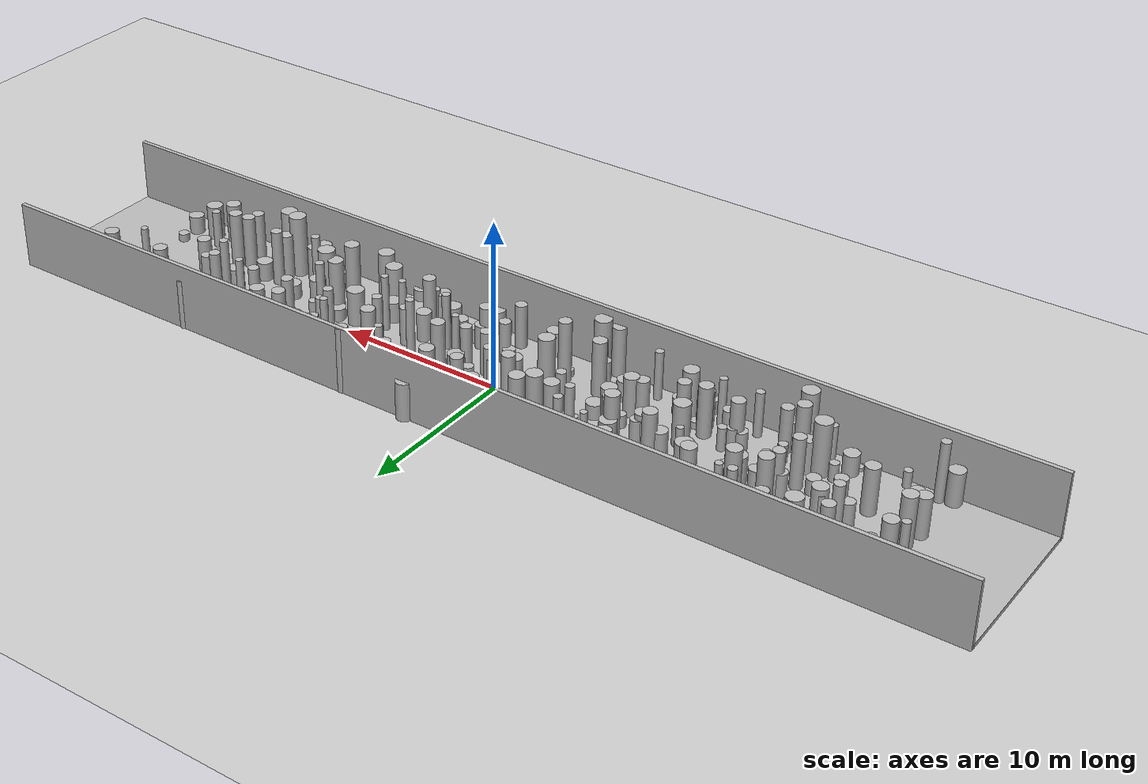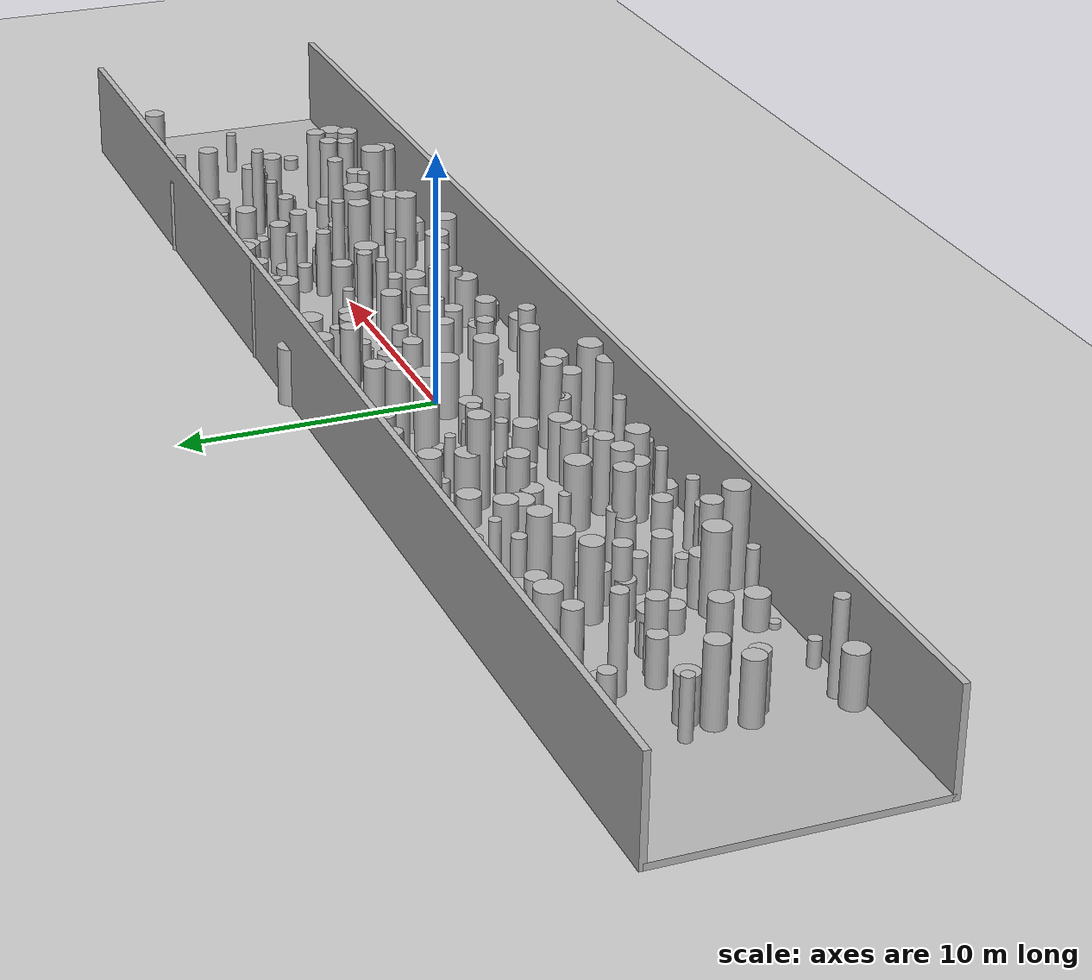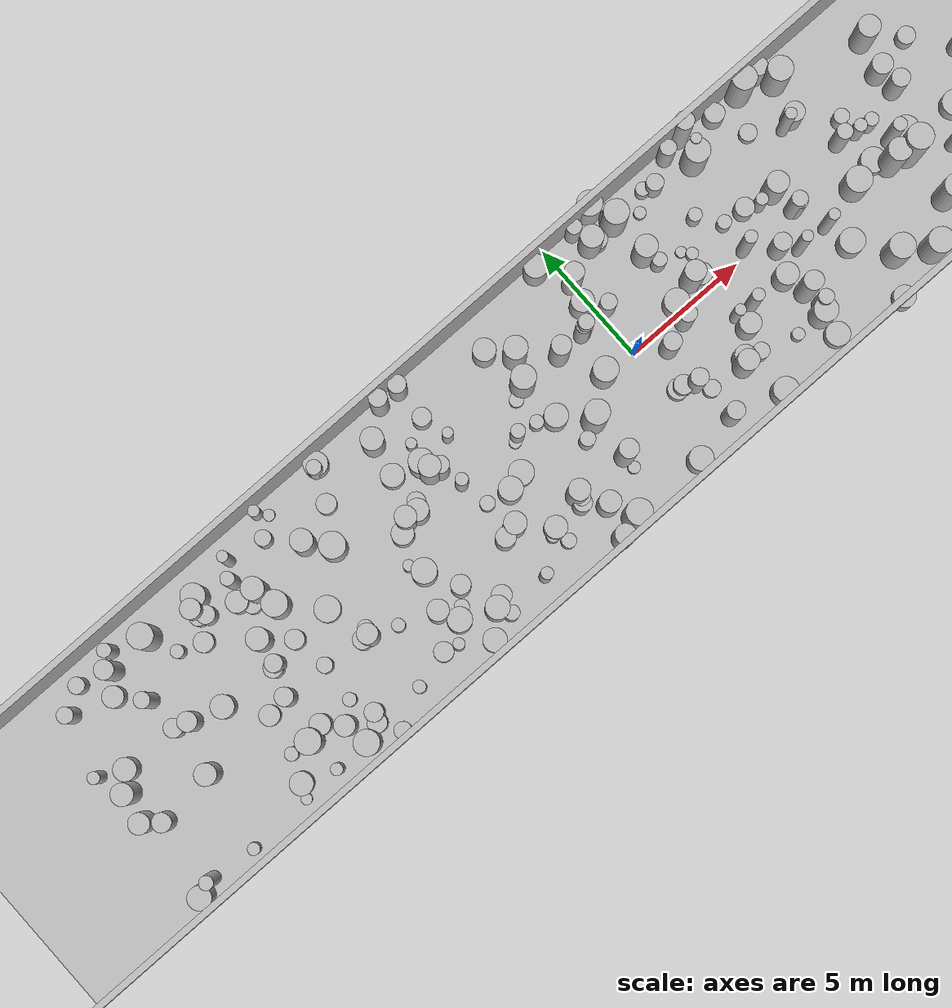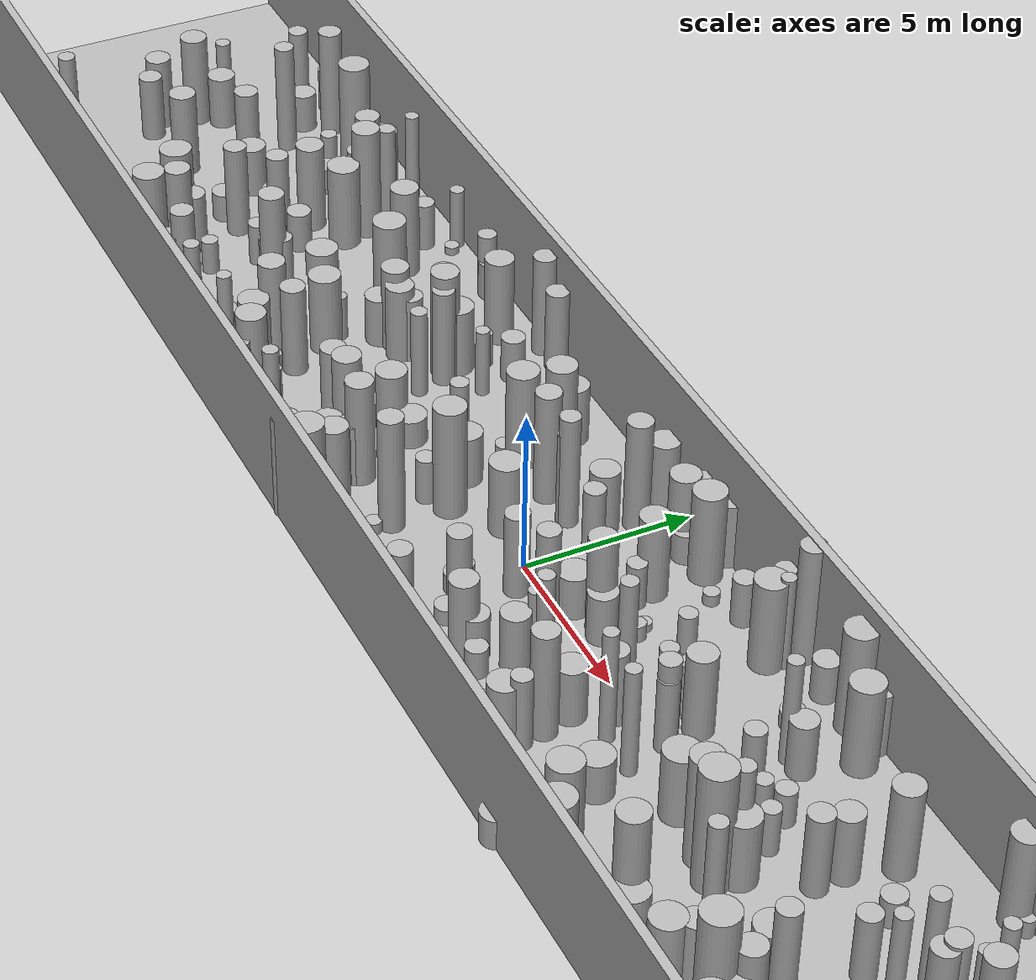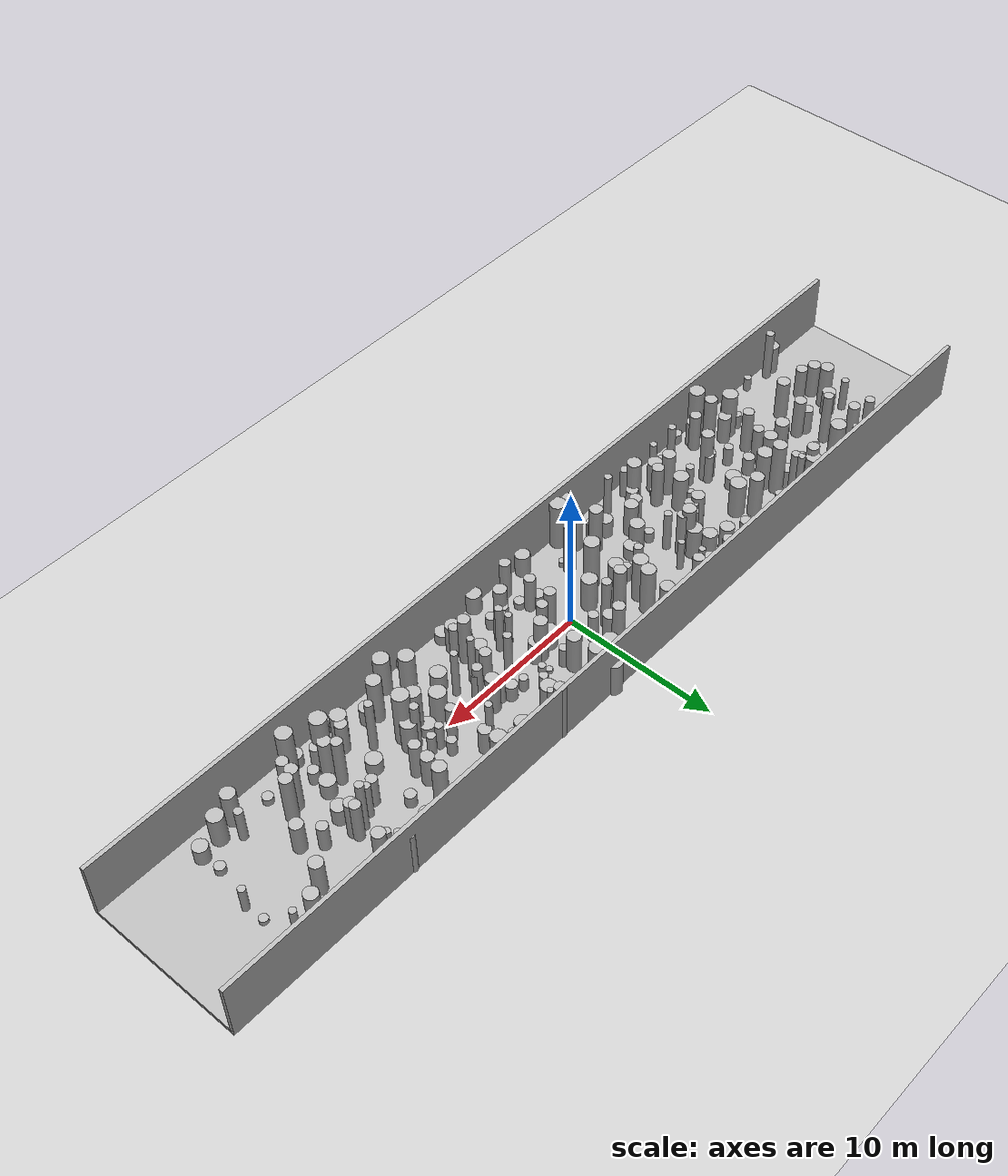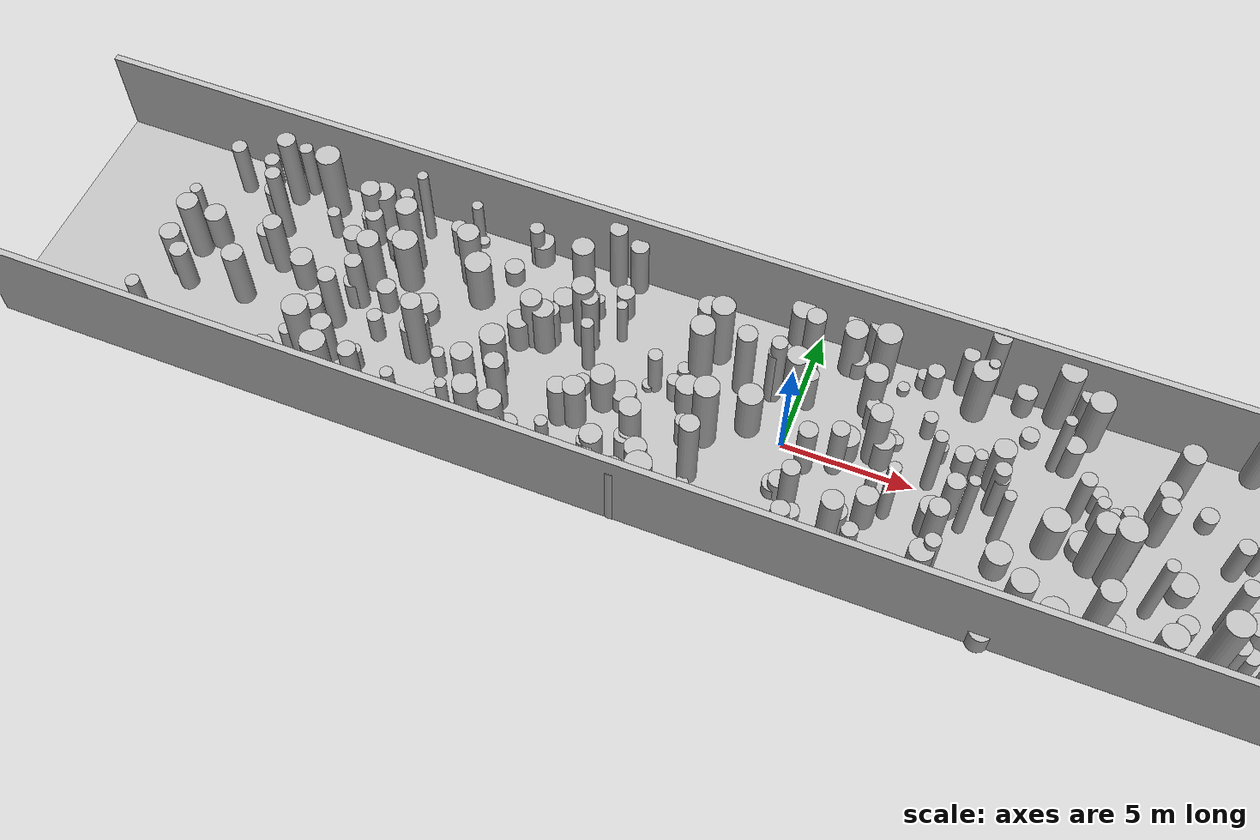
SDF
<?xml version="1.0"?>
<sdf version="1.4">
  <world name="default">
    <gui>
      <camera name="user_camera">
        <pose>-20 -30 40 0 0.66 0.83</pose>
      </camera>
    </gui>
    <include>
      <uri>model://ground_plane</uri>
    </include>
    <include>
      <uri>model://sun</uri>
    </include>
    <scene>
      <shadows>0</shadows>
    </scene>
    <model name="forest">
      <static>true</static>
      <link name="cylinder0">
        <pose>3.4168227689153774 -3.0006204460932207 0.5657098314745399 0 0 0 </pose>
        <visual name="visual">
          <geometry>
            <cylinder>
              <radius>0.3139130072410652</radius>
              <length>1.1314196629490798</length>
            </cylinder>
          </geometry>
        </visual>
        <collision name="collision">
          <geometry>
            <cylinder>
              <radius>0.3139130072410652</radius>
              <length>1.1314196629490798</length>
            </cylinder>
          </geometry>
          <max_contacts>0</max_contacts>
        </collision>
      </link>
      <link name="cylinder1">
        <pose>-10.372897658311741 -2.2514441776818392 1.5751173394590154 0 0 0 </pose>
        <visual name="visual">
          <geometry>
            <cylinder>
              <radius>0.3677514361477285</radius>
              <length>3.150234678918031</length>
            </cylinder>
          </geometry>
        </visual>
        <collision name="collision">
          <geometry>
            <cylinder>
              <radius>0.3677514361477285</radius>
              <length>3.150234678918031</length>
            </cylinder>
          </geometry>
          <max_contacts>0</max_contacts>
        </collision>
      </link>
      <link name="cylinder2">
        <pose>-21.35660350977835 4.323131204310551 1.4216955965478135 0 0 0 </pose>
        <visual name="visual">
          <geometry>
            <cylinder>
              <radius>0.2657979999063645</radius>
              <length>2.843391193095627</length>
            </cylinder>
          </geometry>
        </visual>
        <collision name="collision">
          <geometry>
            <cylinder>
              <radius>0.2657979999063645</radius>
              <length>2.843391193095627</length>
            </cylinder>
          </geometry>
          <max_contacts>0</max_contacts>
        </collision>
      </link>
      <link name="cylinder3">
        <pose>-15.31565662004047 -4.739865447816892 0.4728887307520938 0 0 0 </pose>
        <visual name="visual">
          <geometry>
            <cylinder>
              <radius>0.3305696775943656</radius>
              <length>0.9457774615041876</length>
            </cylinder>
          </geometry>
        </visual>
        <collision name="collision">
          <geometry>
            <cylinder>
              <radius>0.3305696775943656</radius>
              <length>0.9457774615041876</length>
            </cylinder>
          </geometry>
          <max_contacts>0</max_contacts>
        </collision>
      </link>
      <link name="cylinder4">
        <pose>-7.65580942676058 -0.6139596045711126 0.5071746467248583 0 0 0 </pose>
        <visual name="visual">
          <geometry>
            <cylinder>
              <radius>0.28486619734029595</radius>
              <length>1.0143492934497167</length>
            </cylinder>
          </geometry>
        </visual>
        <collision name="collision">
          <geometry>
            <cylinder>
              <radius>0.28486619734029595</radius>
              <length>1.0143492934497167</length>
            </cylinder>
          </geometry>
          <max_contacts>0</max_contacts>
        </collision>
      </link>
      <link name="cylinder5">
        <pose>6.095095211247049 -2.422346213950859 1.8108840715719619 0 0 0 </pose>
        <visual name="visual">
          <geometry>
            <cylinder>
              <radius>0.37031109077982693</radius>
              <length>3.6217681431439237</length>
            </cylinder>
          </geometry>
        </visual>
        <collision name="collision">
          <geometry>
            <cylinder>
              <radius>0.37031109077982693</radius>
              <length>3.6217681431439237</length>
            </cylinder>
          </geometry>
          <max_contacts>0</max_contacts>
        </collision>
      </link>
      <link name="cylinder6">
        <pose>16.30455549652652 4.694991650789337 1.5752967482884006 0 0 0 </pose>
        <visual name="visual">
          <geometry>
            <cylinder>
              <radius>0.4186425243495191</radius>
              <length>3.150593496576801</length>
            </cylinder>
          </geometry>
        </visual>
        <collision name="collision">
          <geometry>
            <cylinder>
              <radius>0.4186425243495191</radius>
              <length>3.150593496576801</length>
            </cylinder>
          </geometry>
          <max_contacts>0</max_contacts>
        </collision>
      </link>
      <link name="cylinder7">
        <pose>12.126960939428884 -0.2747560036739225 1.779856982656079 0 0 0 </pose>
        <visual name="visual">
          <geometry>
            <cylinder>
              <radius>0.2573544955763187</radius>
              <length>3.559713965312158</length>
            </cylinder>
          </geometry>
        </visual>
        <collision name="collision">
          <geometry>
            <cylinder>
              <radius>0.2573544955763187</radius>
              <length>3.559713965312158</length>
            </cylinder>
          </geometry>
          <max_contacts>0</max_contacts>
        </collision>
      </link>
      <link name="cylinder8">
        <pose>-17.6399835858916 -1.1181731487474975 1.6408397410630924 0 0 0 </pose>
        <visual name="visual">
          <geometry>
            <cylinder>
              <radius>0.34879013332269104</radius>
              <length>3.2816794821261848</length>
            </cylinder>
          </geometry>
        </visual>
        <collision name="collision">
          <geometry>
            <cylinder>
              <radius>0.34879013332269104</radius>
              <length>3.2816794821261848</length>
            </cylinder>
          </geometry>
          <max_contacts>0</max_contacts>
        </collision>
      </link>
      <link name="cylinder9">
        <pose>-21.418567242276666 2.0413545910556223 1.9441923723828283 0 0 0 </pose>
        <visual name="visual">
          <geometry>
            <cylinder>
              <radius>0.3000890618956727</radius>
              <length>3.8883847447656565</length>
            </cylinder>
          </geometry>
        </visual>
        <collision name="collision">
          <geometry>
            <cylinder>
              <radius>0.3000890618956727</radius>
              <length>3.8883847447656565</length>
            </cylinder>
          </geometry>
          <max_contacts>0</max_contacts>
        </collision>
      </link>
      <link name="cylinder10">
        <pose>-3.9640936507708737 -4.494682512539475 1.7691035965591073 0 0 0 </pose>
        <visual name="visual">
          <geometry>
            <cylinder>
              <radius>0.4929012030094775</radius>
              <length>3.5382071931182146</length>
            </cylinder>
          </geometry>
        </visual>
        <collision name="collision">
          <geometry>
            <cylinder>
              <radius>0.4929012030094775</radius>
              <length>3.5382071931182146</length>
            </cylinder>
          </geometry>
          <max_contacts>0</max_contacts>
        </collision>
      </link>
      <link name="cylinder11">
        <pose>4.119614725509109 4.248106895456525 0.49777550320334263 0 0 0 </pose>
        <visual name="visual">
          <geometry>
            <cylinder>
              <radius>0.26283163536728527</radius>
              <length>0.9955510064066853</length>
            </cylinder>
          </geometry>
        </visual>
        <collision name="collision">
          <geometry>
            <cylinder>
              <radius>0.26283163536728527</radius>
              <length>0.9955510064066853</length>
            </cylinder>
          </geometry>
          <max_contacts>0</max_contacts>
        </collision>
      </link>
      <link name="cylinder12">
        <pose>2.429946723753762 4.331881481691408 1.3762242734643872 0 0 0 </pose>
        <visual name="visual">
          <geometry>
            <cylinder>
              <radius>0.25629783081989954</radius>
              <length>2.7524485469287745</length>
            </cylinder>
          </geometry>
        </visual>
        <collision name="collision">
          <geometry>
            <cylinder>
              <radius>0.25629783081989954</radius>
              <length>2.7524485469287745</length>
            </cylinder>
          </geometry>
          <max_contacts>0</max_contacts>
        </collision>
      </link>
      <link name="cylinder13">
        <pose>1.6259678344600275 3.950482960120725 0.596414468972401 0 0 0 </pose>
        <visual name="visual">
          <geometry>
            <cylinder>
              <radius>0.39085373932413436</radius>
              <length>1.192828937944802</length>
            </cylinder>
          </geometry>
        </visual>
        <collision name="collision">
          <geometry>
            <cylinder>
              <radius>0.39085373932413436</radius>
              <length>1.192828937944802</length>
            </cylinder>
          </geometry>
          <max_contacts>0</max_contacts>
        </collision>
      </link>
      <link name="cylinder14">
        <pose>-21.72910784840053 3.717128631614173 1.9317601741943404 0 0 0 </pose>
        <visual name="visual">
          <geometry>
            <cylinder>
              <radius>0.3604419685028365</radius>
              <length>3.863520348388681</length>
            </cylinder>
          </geometry>
        </visual>
        <collision name="collision">
          <geometry>
            <cylinder>
              <radius>0.3604419685028365</radius>
              <length>3.863520348388681</length>
            </cylinder>
          </geometry>
          <max_contacts>0</max_contacts>
        </collision>
      </link>
      <link name="cylinder15">
        <pose>-2.8014205256658613 -2.5870234065136155 1.965258638447553 0 0 0 </pose>
        <visual name="visual">
          <geometry>
            <cylinder>
              <radius>0.3665065091192464</radius>
              <length>3.930517276895106</length>
            </cylinder>
          </geometry>
        </visual>
        <collision name="collision">
          <geometry>
            <cylinder>
              <radius>0.3665065091192464</radius>
              <length>3.930517276895106</length>
            </cylinder>
          </geometry>
          <max_contacts>0</max_contacts>
        </collision>
      </link>
      <link name="cylinder16">
        <pose>-8.509159303555986 2.010298377042754 1.2016192523146536 0 0 0 </pose>
        <visual name="visual">
          <geometry>
            <cylinder>
              <radius>0.47469551965957124</radius>
              <length>2.403238504629307</length>
            </cylinder>
          </geometry>
        </visual>
        <collision name="collision">
          <geometry>
            <cylinder>
              <radius>0.47469551965957124</radius>
              <length>2.403238504629307</length>
            </cylinder>
          </geometry>
          <max_contacts>0</max_contacts>
        </collision>
      </link>
      <link name="cylinder17">
        <pose>2.537903652770435 4.062633075450542 1.5659248072147622 0 0 0 </pose>
        <visual name="visual">
          <geometry>
            <cylinder>
              <radius>0.4730240623787522</radius>
              <length>3.1318496144295245</length>
            </cylinder>
          </geometry>
        </visual>
        <collision name="collision">
          <geometry>
            <cylinder>
              <radius>0.4730240623787522</radius>
              <length>3.1318496144295245</length>
            </cylinder>
          </geometry>
          <max_contacts>0</max_contacts>
        </collision>
      </link>
      <link name="cylinder18">
        <pose>9.476005156862094 2.567989246575573 1.771136329113 0 0 0 </pose>
        <visual name="visual">
          <geometry>
            <cylinder>
              <radius>0.21846112876386714</radius>
              <length>3.542272658226</length>
            </cylinder>
          </geometry>
        </visual>
        <collision name="collision">
          <geometry>
            <cylinder>
              <radius>0.21846112876386714</radius>
              <length>3.542272658226</length>
            </cylinder>
          </geometry>
          <max_contacts>0</max_contacts>
        </collision>
      </link>
      <link name="cylinder19">
        <pose>-7.13813193123433 2.1475875548013645 1.2059995553341458 0 0 0 </pose>
        <visual name="visual">
          <geometry>
            <cylinder>
              <radius>0.2048496442567242</radius>
              <length>2.4119991106682916</length>
            </cylinder>
          </geometry>
        </visual>
        <collision name="collision">
          <geometry>
            <cylinder>
              <radius>0.2048496442567242</radius>
              <length>2.4119991106682916</length>
            </cylinder>
          </geometry>
          <max_contacts>0</max_contacts>
        </collision>
      </link>
      <link name="cylinder20">
        <pose>9.98174227509422 -0.7284546494891488 1.1860617621199308 0 0 0 </pose>
        <visual name="visual">
          <geometry>
            <cylinder>
              <radius>0.4957982226751226</radius>
              <length>2.3721235242398615</length>
            </cylinder>
          </geometry>
        </visual>
        <collision name="collision">
          <geometry>
            <cylinder>
              <radius>0.4957982226751226</radius>
              <length>2.3721235242398615</length>
            </cylinder>
          </geometry>
          <max_contacts>0</max_contacts>
        </collision>
      </link>
      <link name="cylinder21">
        <pose>-12.031961741088226 3.194976193978807 0.5398428350440663 0 0 0 </pose>
        <visual name="visual">
          <geometry>
            <cylinder>
              <radius>0.3801661684491565</radius>
              <length>1.0796856700881325</length>
            </cylinder>
          </geometry>
        </visual>
        <collision name="collision">
          <geometry>
            <cylinder>
              <radius>0.3801661684491565</radius>
              <length>1.0796856700881325</length>
            </cylinder>
          </geometry>
          <max_contacts>0</max_contacts>
        </collision>
      </link>
      <link name="cylinder22">
        <pose>17.75844524702019 4.9406119250586915 1.514483509496593 0 0 0 </pose>
        <visual name="visual">
          <geometry>
            <cylinder>
              <radius>0.2611316210934098</radius>
              <length>3.028967018993186</length>
            </cylinder>
          </geometry>
        </visual>
        <collision name="collision">
          <geometry>
            <cylinder>
              <radius>0.2611316210934098</radius>
              <length>3.028967018993186</length>
            </cylinder>
          </geometry>
          <max_contacts>0</max_contacts>
        </collision>
      </link>
      <link name="cylinder23">
        <pose>5.432612022886481 0.19492101263265926 1.8601651168344884 0 0 0 </pose>
        <visual name="visual">
          <geometry>
            <cylinder>
              <radius>0.2423647207048519</radius>
              <length>3.7203302336689767</length>
            </cylinder>
          </geometry>
        </visual>
        <collision name="collision">
          <geometry>
            <cylinder>
              <radius>0.2423647207048519</radius>
              <length>3.7203302336689767</length>
            </cylinder>
          </geometry>
          <max_contacts>0</max_contacts>
        </collision>
      </link>
      <link name="cylinder24">
        <pose>16.97474772034049 1.04251455019953 1.388998019789471 0 0 0 </pose>
        <visual name="visual">
          <geometry>
            <cylinder>
              <radius>0.2256265079048133</radius>
              <length>2.777996039578942</length>
            </cylinder>
          </geometry>
        </visual>
        <collision name="collision">
          <geometry>
            <cylinder>
              <radius>0.2256265079048133</radius>
              <length>2.777996039578942</length>
            </cylinder>
          </geometry>
          <max_contacts>0</max_contacts>
        </collision>
      </link>
      <link name="cylinder25">
        <pose>14.907421635599988 -3.0140926982769365 1.222793909276517 0 0 0 </pose>
        <visual name="visual">
          <geometry>
            <cylinder>
              <radius>0.3680840713682659</radius>
              <length>2.445587818553034</length>
            </cylinder>
          </geometry>
        </visual>
        <collision name="collision">
          <geometry>
            <cylinder>
              <radius>0.3680840713682659</radius>
              <length>2.445587818553034</length>
            </cylinder>
          </geometry>
          <max_contacts>0</max_contacts>
        </collision>
      </link>
      <link name="cylinder26">
        <pose>5.527947056634009 1.3798075787001238 0.576673698230328 0 0 0 </pose>
        <visual name="visual">
          <geometry>
            <cylinder>
              <radius>0.2649422925226506</radius>
              <length>1.153347396460656</length>
            </cylinder>
          </geometry>
        </visual>
        <collision name="collision">
          <geometry>
            <cylinder>
              <radius>0.2649422925226506</radius>
              <length>1.153347396460656</length>
            </cylinder>
          </geometry>
          <max_contacts>0</max_contacts>
        </collision>
      </link>
      <link name="cylinder27">
        <pose>0.30530906758772147 1.8873040653429154 1.1403596677238335 0 0 0 </pose>
        <visual name="visual">
          <geometry>
            <cylinder>
              <radius>0.30975460058401943</radius>
              <length>2.280719335447667</length>
            </cylinder>
          </geometry>
        </visual>
        <collision name="collision">
          <geometry>
            <cylinder>
              <radius>0.30975460058401943</radius>
              <length>2.280719335447667</length>
            </cylinder>
          </geometry>
          <max_contacts>0</max_contacts>
        </collision>
      </link>
      <link name="cylinder28">
        <pose>-22.999633626282684 4.128262922538253 0.8400408961245629 0 0 0 </pose>
        <visual name="visual">
          <geometry>
            <cylinder>
              <radius>0.3103891382681767</radius>
              <length>1.6800817922491258</length>
            </cylinder>
          </geometry>
        </visual>
        <collision name="collision">
          <geometry>
            <cylinder>
              <radius>0.3103891382681767</radius>
              <length>1.6800817922491258</length>
            </cylinder>
          </geometry>
          <max_contacts>0</max_contacts>
        </collision>
      </link>
      <link name="cylinder29">
        <pose>18.137900436876656 2.9549398702739103 0.8520888014592398 0 0 0 </pose>
        <visual name="visual">
          <geometry>
            <cylinder>
              <radius>0.39659908892600876</radius>
              <length>1.7041776029184796</length>
            </cylinder>
          </geometry>
        </visual>
        <collision name="collision">
          <geometry>
            <cylinder>
              <radius>0.39659908892600876</radius>
              <length>1.7041776029184796</length>
            </cylinder>
          </geometry>
          <max_contacts>0</max_contacts>
        </collision>
      </link>
      <link name="cylinder30">
        <pose>-4.834168019107949 -4.76297067830262 1.612533425758893 0 0 0 </pose>
        <visual name="visual">
          <geometry>
            <cylinder>
              <radius>0.3931359872802575</radius>
              <length>3.225066851517786</length>
            </cylinder>
          </geometry>
        </visual>
        <collision name="collision">
          <geometry>
            <cylinder>
              <radius>0.3931359872802575</radius>
              <length>3.225066851517786</length>
            </cylinder>
          </geometry>
          <max_contacts>0</max_contacts>
        </collision>
      </link>
      <link name="cylinder31">
        <pose>4.879031803466521 -3.425241943745214 0.41731307399969575 0 0 0 </pose>
        <visual name="visual">
          <geometry>
            <cylinder>
              <radius>0.23636158090995715</radius>
              <length>0.8346261479993915</length>
            </cylinder>
          </geometry>
        </visual>
        <collision name="collision">
          <geometry>
            <cylinder>
              <radius>0.23636158090995715</radius>
              <length>0.8346261479993915</length>
            </cylinder>
          </geometry>
          <max_contacts>0</max_contacts>
        </collision>
      </link>
      <link name="cylinder32">
        <pose>-9.584879010355568 1.0462139949960854 1.174111556515456 0 0 0 </pose>
        <visual name="visual">
          <geometry>
            <cylinder>
              <radius>0.3442459100977423</radius>
              <length>2.348223113030912</length>
            </cylinder>
          </geometry>
        </visual>
        <collision name="collision">
          <geometry>
            <cylinder>
              <radius>0.3442459100977423</radius>
              <length>2.348223113030912</length>
            </cylinder>
          </geometry>
          <max_contacts>0</max_contacts>
        </collision>
      </link>
      <link name="cylinder33">
        <pose>-8.314321326137335 2.1344865203644954 1.0239917402976537 0 0 0 </pose>
        <visual name="visual">
          <geometry>
            <cylinder>
              <radius>0.22889207087869748</radius>
              <length>2.0479834805953074</length>
            </cylinder>
          </geometry>
        </visual>
        <collision name="collision">
          <geometry>
            <cylinder>
              <radius>0.22889207087869748</radius>
              <length>2.0479834805953074</length>
            </cylinder>
          </geometry>
          <max_contacts>0</max_contacts>
        </collision>
      </link>
      <link name="cylinder34">
        <pose>11.514855932610693 -0.9473922208191068 1.8160114090090107 0 0 0 </pose>
        <visual name="visual">
          <geometry>
            <cylinder>
              <radius>0.43567982473361944</radius>
              <length>3.6320228180180214</length>
            </cylinder>
          </geometry>
        </visual>
        <collision name="collision">
          <geometry>
            <cylinder>
              <radius>0.43567982473361944</radius>
              <length>3.6320228180180214</length>
            </cylinder>
          </geometry>
          <max_contacts>0</max_contacts>
        </collision>
      </link>
      <link name="cylinder35">
        <pose>-13.98275207800716 -1.4099963655659433 1.930059043675803 0 0 0 </pose>
        <visual name="visual">
          <geometry>
            <cylinder>
              <radius>0.3846217041713943</radius>
              <length>3.860118087351606</length>
            </cylinder>
          </geometry>
        </visual>
        <collision name="collision">
          <geometry>
            <cylinder>
              <radius>0.3846217041713943</radius>
              <length>3.860118087351606</length>
            </cylinder>
          </geometry>
          <max_contacts>0</max_contacts>
        </collision>
      </link>
      <link name="cylinder36">
        <pose>0.2807022514431097 -2.0518586225310873 0.41371098489673686 0 0 0 </pose>
        <visual name="visual">
          <geometry>
            <cylinder>
              <radius>0.3976080216409922</radius>
              <length>0.8274219697934737</length>
            </cylinder>
          </geometry>
        </visual>
        <collision name="collision">
          <geometry>
            <cylinder>
              <radius>0.3976080216409922</radius>
              <length>0.8274219697934737</length>
            </cylinder>
          </geometry>
          <max_contacts>0</max_contacts>
        </collision>
      </link>
      <link name="cylinder37">
        <pose>-3.8607344618718216 1.798230171711456 1.6737267998288308 0 0 0 </pose>
        <visual name="visual">
          <geometry>
            <cylinder>
              <radius>0.4647667166601855</radius>
              <length>3.3474535996576615</length>
            </cylinder>
          </geometry>
        </visual>
        <collision name="collision">
          <geometry>
            <cylinder>
              <radius>0.4647667166601855</radius>
              <length>3.3474535996576615</length>
            </cylinder>
          </geometry>
          <max_contacts>0</max_contacts>
        </collision>
      </link>
      <link name="cylinder38">
        <pose>-0.8014173717320894 4.576177597131219 1.1198457528946701 0 0 0 </pose>
        <visual name="visual">
          <geometry>
            <cylinder>
              <radius>0.44384524996406</radius>
              <length>2.2396915057893403</length>
            </cylinder>
          </geometry>
        </visual>
        <collision name="collision">
          <geometry>
            <cylinder>
              <radius>0.44384524996406</radius>
              <length>2.2396915057893403</length>
            </cylinder>
          </geometry>
          <max_contacts>0</max_contacts>
        </collision>
      </link>
      <link name="cylinder39">
        <pose>-16.748765194154092 2.621964411362523 0.8012393157230397 0 0 0 </pose>
        <visual name="visual">
          <geometry>
            <cylinder>
              <radius>0.4158010496673338</radius>
              <length>1.6024786314460795</length>
            </cylinder>
          </geometry>
        </visual>
        <collision name="collision">
          <geometry>
            <cylinder>
              <radius>0.4158010496673338</radius>
              <length>1.6024786314460795</length>
            </cylinder>
          </geometry>
          <max_contacts>0</max_contacts>
        </collision>
      </link>
      <link name="cylinder40">
        <pose>4.509219674056563 4.077539946630672 0.853091718121875 0 0 0 </pose>
        <visual name="visual">
          <geometry>
            <cylinder>
              <radius>0.32271097277579086</radius>
              <length>1.70618343624375</length>
            </cylinder>
          </geometry>
        </visual>
        <collision name="collision">
          <geometry>
            <cylinder>
              <radius>0.32271097277579086</radius>
              <length>1.70618343624375</length>
            </cylinder>
          </geometry>
          <max_contacts>0</max_contacts>
        </collision>
      </link>
      <link name="cylinder41">
        <pose>1.2245320372545265 -2.8336640941562754 0.3683639810047978 0 0 0 </pose>
        <visual name="visual">
          <geometry>
            <cylinder>
              <radius>0.327157093566002</radius>
              <length>0.7367279620095956</length>
            </cylinder>
          </geometry>
        </visual>
        <collision name="collision">
          <geometry>
            <cylinder>
              <radius>0.327157093566002</radius>
              <length>0.7367279620095956</length>
            </cylinder>
          </geometry>
          <max_contacts>0</max_contacts>
        </collision>
      </link>
      <link name="cylinder42">
        <pose>-4.168211580672331 3.539522852405357 1.0555643035714661 0 0 0 </pose>
        <visual name="visual">
          <geometry>
            <cylinder>
              <radius>0.4317310562778898</radius>
              <length>2.1111286071429323</length>
            </cylinder>
          </geometry>
        </visual>
        <collision name="collision">
          <geometry>
            <cylinder>
              <radius>0.4317310562778898</radius>
              <length>2.1111286071429323</length>
            </cylinder>
          </geometry>
          <max_contacts>0</max_contacts>
        </collision>
      </link>
      <link name="cylinder43">
        <pose>-19.71796774710507 0.3110879446256192 0.7624264279020374 0 0 0 </pose>
        <visual name="visual">
          <geometry>
            <cylinder>
              <radius>0.2364860129090609</radius>
              <length>1.5248528558040748</length>
            </cylinder>
          </geometry>
        </visual>
        <collision name="collision">
          <geometry>
            <cylinder>
              <radius>0.2364860129090609</radius>
              <length>1.5248528558040748</length>
            </cylinder>
          </geometry>
          <max_contacts>0</max_contacts>
        </collision>
      </link>
      <link name="cylinder44">
        <pose>-17.012740371954205 1.0431191071362802 1.5581251016779272 0 0 0 </pose>
        <visual name="visual">
          <geometry>
            <cylinder>
              <radius>0.4273241364926528</radius>
              <length>3.1162502033558543</length>
            </cylinder>
          </geometry>
        </visual>
        <collision name="collision">
          <geometry>
            <cylinder>
              <radius>0.4273241364926528</radius>
              <length>3.1162502033558543</length>
            </cylinder>
          </geometry>
          <max_contacts>0</max_contacts>
        </collision>
      </link>
      <link name="cylinder45">
        <pose>12.477127357572357 -0.45924616195239043 1.1842098432579775 0 0 0 </pose>
        <visual name="visual">
          <geometry>
            <cylinder>
              <radius>0.4751936288855037</radius>
              <length>2.368419686515955</length>
            </cylinder>
          </geometry>
        </visual>
        <collision name="collision">
          <geometry>
            <cylinder>
              <radius>0.4751936288855037</radius>
              <length>2.368419686515955</length>
            </cylinder>
          </geometry>
          <max_contacts>0</max_contacts>
        </collision>
      </link>
      <link name="cylinder46">
        <pose>-2.786542864333864 -3.1168611972613824 0.3127594682873085 0 0 0 </pose>
        <visual name="visual">
          <geometry>
            <cylinder>
              <radius>0.23314054018545585</radius>
              <length>0.625518936574617</length>
            </cylinder>
          </geometry>
        </visual>
        <collision name="collision">
          <geometry>
            <cylinder>
              <radius>0.23314054018545585</radius>
              <length>0.625518936574617</length>
            </cylinder>
          </geometry>
          <max_contacts>0</max_contacts>
        </collision>
      </link>
      <link name="cylinder47">
        <pose>24.444030777441213 -3.407347500628516 0.6774231674197793 0 0 0 </pose>
        <visual name="visual">
          <geometry>
            <cylinder>
              <radius>0.44775015131962803</radius>
              <length>1.3548463348395585</length>
            </cylinder>
          </geometry>
        </visual>
        <collision name="collision">
          <geometry>
            <cylinder>
              <radius>0.44775015131962803</radius>
              <length>1.3548463348395585</length>
            </cylinder>
          </geometry>
          <max_contacts>0</max_contacts>
        </collision>
      </link>
      <link name="cylinder48">
        <pose>-3.405470062892384 2.7421743650802366 1.7738745624559829 0 0 0 </pose>
        <visual name="visual">
          <geometry>
            <cylinder>
              <radius>0.44209173592323403</radius>
              <length>3.5477491249119657</length>
            </cylinder>
          </geometry>
        </visual>
        <collision name="collision">
          <geometry>
            <cylinder>
              <radius>0.44209173592323403</radius>
              <length>3.5477491249119657</length>
            </cylinder>
          </geometry>
          <max_contacts>0</max_contacts>
        </collision>
      </link>
      <link name="cylinder49">
        <pose>3.7187804958886446 1.644182984014714 0.2393058109263186 0 0 0 </pose>
        <visual name="visual">
          <geometry>
            <cylinder>
              <radius>0.20761023267116188</radius>
              <length>0.4786116218526372</length>
            </cylinder>
          </geometry>
        </visual>
        <collision name="collision">
          <geometry>
            <cylinder>
              <radius>0.20761023267116188</radius>
              <length>0.4786116218526372</length>
            </cylinder>
          </geometry>
          <max_contacts>0</max_contacts>
        </collision>
      </link>
      <link name="cylinder50">
        <pose>-8.241870612352987 4.616287864682828 1.7652205598682105 0 0 0 </pose>
        <visual name="visual">
          <geometry>
            <cylinder>
              <radius>0.3414705632696613</radius>
              <length>3.530441119736421</length>
            </cylinder>
          </geometry>
        </visual>
        <collision name="collision">
          <geometry>
            <cylinder>
              <radius>0.3414705632696613</radius>
              <length>3.530441119736421</length>
            </cylinder>
          </geometry>
          <max_contacts>0</max_contacts>
        </collision>
      </link>
      <link name="cylinder51">
        <pose>3.0849625496992488 -4.646589702898501 0.7969033168566544 0 0 0 </pose>
        <visual name="visual">
          <geometry>
            <cylinder>
              <radius>0.47713429524977524</radius>
              <length>1.5938066337133088</length>
            </cylinder>
          </geometry>
        </visual>
        <collision name="collision">
          <geometry>
            <cylinder>
              <radius>0.47713429524977524</radius>
              <length>1.5938066337133088</length>
            </cylinder>
          </geometry>
          <max_contacts>0</max_contacts>
        </collision>
      </link>
      <link name="cylinder52">
        <pose>7.635228746074446 1.0870725946404933 1.413383033654066 0 0 0 </pose>
        <visual name="visual">
          <geometry>
            <cylinder>
              <radius>0.41474855454471704</radius>
              <length>2.826766067308132</length>
            </cylinder>
          </geometry>
        </visual>
        <collision name="collision">
          <geometry>
            <cylinder>
              <radius>0.41474855454471704</radius>
              <length>2.826766067308132</length>
            </cylinder>
          </geometry>
          <max_contacts>0</max_contacts>
        </collision>
      </link>
      <link name="cylinder53">
        <pose>-1.4025854770964337 0.1271315581665391 1.2750346920651203 0 0 0 </pose>
        <visual name="visual">
          <geometry>
            <cylinder>
              <radius>0.4735796043228775</radius>
              <length>2.5500693841302406</length>
            </cylinder>
          </geometry>
        </visual>
        <collision name="collision">
          <geometry>
            <cylinder>
              <radius>0.4735796043228775</radius>
              <length>2.5500693841302406</length>
            </cylinder>
          </geometry>
          <max_contacts>0</max_contacts>
        </collision>
      </link>
      <link name="cylinder54">
        <pose>16.28224763181415 0.6509675340185703 1.1512908590575814 0 0 0 </pose>
        <visual name="visual">
          <geometry>
            <cylinder>
              <radius>0.3228887253956194</radius>
              <length>2.302581718115163</length>
            </cylinder>
          </geometry>
        </visual>
        <collision name="collision">
          <geometry>
            <cylinder>
              <radius>0.3228887253956194</radius>
              <length>2.302581718115163</length>
            </cylinder>
          </geometry>
          <max_contacts>0</max_contacts>
        </collision>
      </link>
      <link name="cylinder55">
        <pose>13.473698099883038 1.006953871160917 1.3632850253873994 0 0 0 </pose>
        <visual name="visual">
          <geometry>
            <cylinder>
              <radius>0.34761580975982925</radius>
              <length>2.7265700507747987</length>
            </cylinder>
          </geometry>
        </visual>
        <collision name="collision">
          <geometry>
            <cylinder>
              <radius>0.34761580975982925</radius>
              <length>2.7265700507747987</length>
            </cylinder>
          </geometry>
          <max_contacts>0</max_contacts>
        </collision>
      </link>
      <link name="cylinder56">
        <pose>18.175802188430886 0.09654596366287116 0.7219304504183779 0 0 0 </pose>
        <visual name="visual">
          <geometry>
            <cylinder>
              <radius>0.45428353367251617</radius>
              <length>1.4438609008367558</length>
            </cylinder>
          </geometry>
        </visual>
        <collision name="collision">
          <geometry>
            <cylinder>
              <radius>0.45428353367251617</radius>
              <length>1.4438609008367558</length>
            </cylinder>
          </geometry>
          <max_contacts>0</max_contacts>
        </collision>
      </link>
      <link name="cylinder57">
        <pose>-15.966854620602138 2.4335190814512897 1.9659533005793128 0 0 0 </pose>
        <visual name="visual">
          <geometry>
            <cylinder>
              <radius>0.42633022457370945</radius>
              <length>3.9319066011586257</length>
            </cylinder>
          </geometry>
        </visual>
        <collision name="collision">
          <geometry>
            <cylinder>
              <radius>0.42633022457370945</radius>
              <length>3.9319066011586257</length>
            </cylinder>
          </geometry>
          <max_contacts>0</max_contacts>
        </collision>
      </link>
      <link name="cylinder58">
        <pose>9.955069784097688 2.6583486859823937 0.9913598653913777 0 0 0 </pose>
        <visual name="visual">
          <geometry>
            <cylinder>
              <radius>0.3821587422730991</radius>
              <length>1.9827197307827553</length>
            </cylinder>
          </geometry>
        </visual>
        <collision name="collision">
          <geometry>
            <cylinder>
              <radius>0.3821587422730991</radius>
              <length>1.9827197307827553</length>
            </cylinder>
          </geometry>
          <max_contacts>0</max_contacts>
        </collision>
      </link>
      <link name="cylinder59">
        <pose>4.27891711785789 -1.5129729196351138 1.8169500176617168 0 0 0 </pose>
        <visual name="visual">
          <geometry>
            <cylinder>
              <radius>0.23445608639623608</radius>
              <length>3.6339000353234336</length>
            </cylinder>
          </geometry>
        </visual>
        <collision name="collision">
          <geometry>
            <cylinder>
              <radius>0.23445608639623608</radius>
              <length>3.6339000353234336</length>
            </cylinder>
          </geometry>
          <max_contacts>0</max_contacts>
        </collision>
      </link>
      <link name="cylinder60">
        <pose>7.820291985153808 0.0696702242743763 1.2730377012281773 0 0 0 </pose>
        <visual name="visual">
          <geometry>
            <cylinder>
              <radius>0.29449439438048525</radius>
              <length>2.5460754024563546</length>
            </cylinder>
          </geometry>
        </visual>
        <collision name="collision">
          <geometry>
            <cylinder>
              <radius>0.29449439438048525</radius>
              <length>2.5460754024563546</length>
            </cylinder>
          </geometry>
          <max_contacts>0</max_contacts>
        </collision>
      </link>
      <link name="cylinder61">
        <pose>1.0588627270553594 -4.0436026388371396 1.4500712544282837 0 0 0 </pose>
        <visual name="visual">
          <geometry>
            <cylinder>
              <radius>0.3393122257825558</radius>
              <length>2.9001425088565673</length>
            </cylinder>
          </geometry>
        </visual>
        <collision name="collision">
          <geometry>
            <cylinder>
              <radius>0.3393122257825558</radius>
              <length>2.9001425088565673</length>
            </cylinder>
          </geometry>
          <max_contacts>0</max_contacts>
        </collision>
      </link>
      <link name="cylinder62">
        <pose>6.194814364536061 3.8144096999039387 1.5415645126009914 0 0 0 </pose>
        <visual name="visual">
          <geometry>
            <cylinder>
              <radius>0.4681434991191864</radius>
              <length>3.0831290252019827</length>
            </cylinder>
          </geometry>
        </visual>
        <collision name="collision">
          <geometry>
            <cylinder>
              <radius>0.4681434991191864</radius>
              <length>3.0831290252019827</length>
            </cylinder>
          </geometry>
          <max_contacts>0</max_contacts>
        </collision>
      </link>
      <link name="cylinder63">
        <pose>-7.81830034674989 -3.96246343868367 1.5871151356668565 0 0 0 </pose>
        <visual name="visual">
          <geometry>
            <cylinder>
              <radius>0.23331854728300358</radius>
              <length>3.174230271333713</length>
            </cylinder>
          </geometry>
        </visual>
        <collision name="collision">
          <geometry>
            <cylinder>
              <radius>0.23331854728300358</radius>
              <length>3.174230271333713</length>
            </cylinder>
          </geometry>
          <max_contacts>0</max_contacts>
        </collision>
      </link>
      <link name="cylinder64">
        <pose>-22.082502001315603 -4.403343819644552 0.613707244978996 0 0 0 </pose>
        <visual name="visual">
          <geometry>
            <cylinder>
              <radius>0.2333413649471318</radius>
              <length>1.227414489957992</length>
            </cylinder>
          </geometry>
        </visual>
        <collision name="collision">
          <geometry>
            <cylinder>
              <radius>0.2333413649471318</radius>
              <length>1.227414489957992</length>
            </cylinder>
          </geometry>
          <max_contacts>0</max_contacts>
        </collision>
      </link>
      <link name="cylinder65">
        <pose>-8.311809174564782 2.8007965697433077 0.670392578374513 0 0 0 </pose>
        <visual name="visual">
          <geometry>
            <cylinder>
              <radius>0.2066680580027065</radius>
              <length>1.340785156749026</length>
            </cylinder>
          </geometry>
        </visual>
        <collision name="collision">
          <geometry>
            <cylinder>
              <radius>0.2066680580027065</radius>
              <length>1.340785156749026</length>
            </cylinder>
          </geometry>
          <max_contacts>0</max_contacts>
        </collision>
      </link>
      <link name="cylinder66">
        <pose>-17.37058964714589 -2.6521520822557063 1.0960785140175782 0 0 0 </pose>
        <visual name="visual">
          <geometry>
            <cylinder>
              <radius>0.3983850361801018</radius>
              <length>2.1921570280351563</length>
            </cylinder>
          </geometry>
        </visual>
        <collision name="collision">
          <geometry>
            <cylinder>
              <radius>0.3983850361801018</radius>
              <length>2.1921570280351563</length>
            </cylinder>
          </geometry>
          <max_contacts>0</max_contacts>
        </collision>
      </link>
      <link name="cylinder67">
        <pose>-9.769559506569225 0.7704495770269446 1.343385655164318 0 0 0 </pose>
        <visual name="visual">
          <geometry>
            <cylinder>
              <radius>0.4213548860620411</radius>
              <length>2.686771310328636</length>
            </cylinder>
          </geometry>
        </visual>
        <collision name="collision">
          <geometry>
            <cylinder>
              <radius>0.4213548860620411</radius>
              <length>2.686771310328636</length>
            </cylinder>
          </geometry>
          <max_contacts>0</max_contacts>
        </collision>
      </link>
      <link name="cylinder68">
        <pose>-10.253609969160799 0.8501133190586216 1.4957817800127082 0 0 0 </pose>
        <visual name="visual">
          <geometry>
            <cylinder>
              <radius>0.4072376539695209</radius>
              <length>2.9915635600254165</length>
            </cylinder>
          </geometry>
        </visual>
        <collision name="collision">
          <geometry>
            <cylinder>
              <radius>0.4072376539695209</radius>
              <length>2.9915635600254165</length>
            </cylinder>
          </geometry>
          <max_contacts>0</max_contacts>
        </collision>
      </link>
      <link name="cylinder69">
        <pose>0.8977024724262535 -2.301481938823 1.36658357312586 0 0 0 </pose>
        <visual name="visual">
          <geometry>
            <cylinder>
              <radius>0.3370675886313821</radius>
              <length>2.73316714625172</length>
            </cylinder>
          </geometry>
        </visual>
        <collision name="collision">
          <geometry>
            <cylinder>
              <radius>0.3370675886313821</radius>
              <length>2.73316714625172</length>
            </cylinder>
          </geometry>
          <max_contacts>0</max_contacts>
        </collision>
      </link>
      <link name="cylinder70">
        <pose>-6.397800764020982 -2.899767563911607 0.7355151845437955 0 0 0 </pose>
        <visual name="visual">
          <geometry>
            <cylinder>
              <radius>0.42835825013344647</radius>
              <length>1.471030369087591</length>
            </cylinder>
          </geometry>
        </visual>
        <collision name="collision">
          <geometry>
            <cylinder>
              <radius>0.42835825013344647</radius>
              <length>1.471030369087591</length>
            </cylinder>
          </geometry>
          <max_contacts>0</max_contacts>
        </collision>
      </link>
      <link name="cylinder71">
        <pose>11.935221255808806 0.6405763827183133 0.826655675524236 0 0 0 </pose>
        <visual name="visual">
          <geometry>
            <cylinder>
              <radius>0.2604943909857404</radius>
              <length>1.653311351048472</length>
            </cylinder>
          </geometry>
        </visual>
        <collision name="collision">
          <geometry>
            <cylinder>
              <radius>0.2604943909857404</radius>
              <length>1.653311351048472</length>
            </cylinder>
          </geometry>
          <max_contacts>0</max_contacts>
        </collision>
      </link>
      <link name="cylinder72">
        <pose>12.205963857380482 -3.213685060846325 1.6967089766937846 0 0 0 </pose>
        <visual name="visual">
          <geometry>
            <cylinder>
              <radius>0.4337033851453723</radius>
              <length>3.3934179533875692</length>
            </cylinder>
          </geometry>
        </visual>
        <collision name="collision">
          <geometry>
            <cylinder>
              <radius>0.4337033851453723</radius>
              <length>3.3934179533875692</length>
            </cylinder>
          </geometry>
          <max_contacts>0</max_contacts>
        </collision>
      </link>
      <link name="cylinder73">
        <pose>15.072860414491757 2.146677233310906 0.5403019122151448 0 0 0 </pose>
        <visual name="visual">
          <geometry>
            <cylinder>
              <radius>0.34055995838630576</radius>
              <length>1.0806038244302896</length>
            </cylinder>
          </geometry>
        </visual>
        <collision name="collision">
          <geometry>
            <cylinder>
              <radius>0.34055995838630576</radius>
              <length>1.0806038244302896</length>
            </cylinder>
          </geometry>
          <max_contacts>0</max_contacts>
        </collision>
      </link>
      <link name="cylinder74">
        <pose>-15.814036391748687 -3.9410867435343544 1.0164899861445449 0 0 0 </pose>
        <visual name="visual">
          <geometry>
            <cylinder>
              <radius>0.3721718367374985</radius>
              <length>2.0329799722890898</length>
            </cylinder>
          </geometry>
        </visual>
        <collision name="collision">
          <geometry>
            <cylinder>
              <radius>0.3721718367374985</radius>
              <length>2.0329799722890898</length>
            </cylinder>
          </geometry>
          <max_contacts>0</max_contacts>
        </collision>
      </link>
      <link name="cylinder75">
        <pose>-6.749490382746476 -0.8293490692678436 1.1113797536738117 0 0 0 </pose>
        <visual name="visual">
          <geometry>
            <cylinder>
              <radius>0.45238148765169817</radius>
              <length>2.2227595073476234</length>
            </cylinder>
          </geometry>
        </visual>
        <collision name="collision">
          <geometry>
            <cylinder>
              <radius>0.45238148765169817</radius>
              <length>2.2227595073476234</length>
            </cylinder>
          </geometry>
          <max_contacts>0</max_contacts>
        </collision>
      </link>
      <link name="cylinder76">
        <pose>-11.383243736141392 4.5109272070521005 0.7206859160088545 0 0 0 </pose>
        <visual name="visual">
          <geometry>
            <cylinder>
              <radius>0.46101447124008627</radius>
              <length>1.441371832017709</length>
            </cylinder>
          </geometry>
        </visual>
        <collision name="collision">
          <geometry>
            <cylinder>
              <radius>0.46101447124008627</radius>
              <length>1.441371832017709</length>
            </cylinder>
          </geometry>
          <max_contacts>0</max_contacts>
        </collision>
      </link>
      <link name="cylinder77">
        <pose>6.413894477884785 4.16249851608033 1.5841606587794075 0 0 0 </pose>
        <visual name="visual">
          <geometry>
            <cylinder>
              <radius>0.20335564849784107</radius>
              <length>3.168321317558815</length>
            </cylinder>
          </geometry>
        </visual>
        <collision name="collision">
          <geometry>
            <cylinder>
              <radius>0.20335564849784107</radius>
              <length>3.168321317558815</length>
            </cylinder>
          </geometry>
          <max_contacts>0</max_contacts>
        </collision>
      </link>
      <link name="cylinder78">
        <pose>-18.608237049293574 2.349809017381528 0.5510838272784618 0 0 0 </pose>
        <visual name="visual">
          <geometry>
            <cylinder>
              <radius>0.3822267673320422</radius>
              <length>1.1021676545569237</length>
            </cylinder>
          </geometry>
        </visual>
        <collision name="collision">
          <geometry>
            <cylinder>
              <radius>0.3822267673320422</radius>
              <length>1.1021676545569237</length>
            </cylinder>
          </geometry>
          <max_contacts>0</max_contacts>
        </collision>
      </link>
      <link name="cylinder79">
        <pose>-14.160204888733425 4.617581358205619 1.1128946065807324 0 0 0 </pose>
        <visual name="visual">
          <geometry>
            <cylinder>
              <radius>0.21860928002505953</radius>
              <length>2.2257892131614647</length>
            </cylinder>
          </geometry>
        </visual>
        <collision name="collision">
          <geometry>
            <cylinder>
              <radius>0.21860928002505953</radius>
              <length>2.2257892131614647</length>
            </cylinder>
          </geometry>
          <max_contacts>0</max_contacts>
        </collision>
      </link>
      <link name="cylinder80">
        <pose>18.984623782332037 -2.931461088920048 1.6807927914078105 0 0 0 </pose>
        <visual name="visual">
          <geometry>
            <cylinder>
              <radius>0.3454384419791381</radius>
              <length>3.361585582815621</length>
            </cylinder>
          </geometry>
        </visual>
        <collision name="collision">
          <geometry>
            <cylinder>
              <radius>0.3454384419791381</radius>
              <length>3.361585582815621</length>
            </cylinder>
          </geometry>
          <max_contacts>0</max_contacts>
        </collision>
      </link>
      <link name="cylinder81">
        <pose>11.259170685666504 1.459962182327608 0.6680011993114968 0 0 0 </pose>
        <visual name="visual">
          <geometry>
            <cylinder>
              <radius>0.2894031104982382</radius>
              <length>1.3360023986229936</length>
            </cylinder>
          </geometry>
        </visual>
        <collision name="collision">
          <geometry>
            <cylinder>
              <radius>0.2894031104982382</radius>
              <length>1.3360023986229936</length>
            </cylinder>
          </geometry>
          <max_contacts>0</max_contacts>
        </collision>
      </link>
      <link name="cylinder82">
        <pose>-7.377317613793856 4.605964793982389 1.4357350175502868 0 0 0 </pose>
        <visual name="visual">
          <geometry>
            <cylinder>
              <radius>0.34700452912200364</radius>
              <length>2.8714700351005735</length>
            </cylinder>
          </geometry>
        </visual>
        <collision name="collision">
          <geometry>
            <cylinder>
              <radius>0.34700452912200364</radius>
              <length>2.8714700351005735</length>
            </cylinder>
          </geometry>
          <max_contacts>0</max_contacts>
        </collision>
      </link>
      <link name="cylinder83">
        <pose>-18.108542652122683 3.4148444649810408 1.445654301262922 0 0 0 </pose>
        <visual name="visual">
          <geometry>
            <cylinder>
              <radius>0.38112671923198294</radius>
              <length>2.891308602525844</length>
            </cylinder>
          </geometry>
        </visual>
        <collision name="collision">
          <geometry>
            <cylinder>
              <radius>0.38112671923198294</radius>
              <length>2.891308602525844</length>
            </cylinder>
          </geometry>
          <max_contacts>0</max_contacts>
        </collision>
      </link>
      <link name="cylinder84">
        <pose>-16.07810474643923 0.25014213677787644 0.7625150647929921 0 0 0 </pose>
        <visual name="visual">
          <geometry>
            <cylinder>
              <radius>0.37070595839633025</radius>
              <length>1.5250301295859843</length>
            </cylinder>
          </geometry>
        </visual>
        <collision name="collision">
          <geometry>
            <cylinder>
              <radius>0.37070595839633025</radius>
              <length>1.5250301295859843</length>
            </cylinder>
          </geometry>
          <max_contacts>0</max_contacts>
        </collision>
      </link>
      <link name="cylinder85">
        <pose>-18.12529728588368 3.1314375955831135 0.7846715255426591 0 0 0 </pose>
        <visual name="visual">
          <geometry>
            <cylinder>
              <radius>0.35187008169221745</radius>
              <length>1.5693430510853181</length>
            </cylinder>
          </geometry>
        </visual>
        <collision name="collision">
          <geometry>
            <cylinder>
              <radius>0.35187008169221745</radius>
              <length>1.5693430510853181</length>
            </cylinder>
          </geometry>
          <max_contacts>0</max_contacts>
        </collision>
      </link>
      <link name="cylinder86">
        <pose>7.76864987697671 0.11340664307148973 1.5410273927857283 0 0 0 </pose>
        <visual name="visual">
          <geometry>
            <cylinder>
              <radius>0.29703365670510856</radius>
              <length>3.0820547855714566</length>
            </cylinder>
          </geometry>
        </visual>
        <collision name="collision">
          <geometry>
            <cylinder>
              <radius>0.29703365670510856</radius>
              <length>3.0820547855714566</length>
            </cylinder>
          </geometry>
          <max_contacts>0</max_contacts>
        </collision>
      </link>
      <link name="cylinder87">
        <pose>5.546138668723188 4.619650474758611 1.3127551031969038 0 0 0 </pose>
        <visual name="visual">
          <geometry>
            <cylinder>
              <radius>0.3052132891249326</radius>
              <length>2.6255102063938076</length>
            </cylinder>
          </geometry>
        </visual>
        <collision name="collision">
          <geometry>
            <cylinder>
              <radius>0.3052132891249326</radius>
              <length>2.6255102063938076</length>
            </cylinder>
          </geometry>
          <max_contacts>0</max_contacts>
        </collision>
      </link>
      <link name="cylinder88">
        <pose>6.953928481721544 1.0564743337878815 0.9945678353152073 0 0 0 </pose>
        <visual name="visual">
          <geometry>
            <cylinder>
              <radius>0.2310721976853025</radius>
              <length>1.9891356706304146</length>
            </cylinder>
          </geometry>
        </visual>
        <collision name="collision">
          <geometry>
            <cylinder>
              <radius>0.2310721976853025</radius>
              <length>1.9891356706304146</length>
            </cylinder>
          </geometry>
          <max_contacts>0</max_contacts>
        </collision>
      </link>
      <link name="cylinder89">
        <pose>3.6107220959592112 -1.4479142739139004 1.2920930081545208 0 0 0 </pose>
        <visual name="visual">
          <geometry>
            <cylinder>
              <radius>0.21086694698652492</radius>
              <length>2.5841860163090415</length>
            </cylinder>
          </geometry>
        </visual>
        <collision name="collision">
          <geometry>
            <cylinder>
              <radius>0.21086694698652492</radius>
              <length>2.5841860163090415</length>
            </cylinder>
          </geometry>
          <max_contacts>0</max_contacts>
        </collision>
      </link>
      <link name="cylinder90">
        <pose>-16.379598077183523 2.2488449342389805 0.5465454976978354 0 0 0 </pose>
        <visual name="visual">
          <geometry>
            <cylinder>
              <radius>0.38060296094125545</radius>
              <length>1.093090995395671</length>
            </cylinder>
          </geometry>
        </visual>
        <collision name="collision">
          <geometry>
            <cylinder>
              <radius>0.38060296094125545</radius>
              <length>1.093090995395671</length>
            </cylinder>
          </geometry>
          <max_contacts>0</max_contacts>
        </collision>
      </link>
      <link name="cylinder91">
        <pose>10.020918655173524 4.733958965947425 1.101997239881362 0 0 0 </pose>
        <visual name="visual">
          <geometry>
            <cylinder>
              <radius>0.35770249806429677</radius>
              <length>2.203994479762724</length>
            </cylinder>
          </geometry>
        </visual>
        <collision name="collision">
          <geometry>
            <cylinder>
              <radius>0.35770249806429677</radius>
              <length>2.203994479762724</length>
            </cylinder>
          </geometry>
          <max_contacts>0</max_contacts>
        </collision>
      </link>
      <link name="cylinder92">
        <pose>-3.7743865474174356 0.08616136112998607 0.9405995916820917 0 0 0 </pose>
        <visual name="visual">
          <geometry>
            <cylinder>
              <radius>0.44745407672025383</radius>
              <length>1.8811991833641835</length>
            </cylinder>
          </geometry>
        </visual>
        <collision name="collision">
          <geometry>
            <cylinder>
              <radius>0.44745407672025383</radius>
              <length>1.8811991833641835</length>
            </cylinder>
          </geometry>
          <max_contacts>0</max_contacts>
        </collision>
      </link>
      <link name="cylinder93">
        <pose>24.363349281199035 -2.141585468703803 0.3630129723596617 0 0 0 </pose>
        <visual name="visual">
          <geometry>
            <cylinder>
              <radius>0.32144948191967604</radius>
              <length>0.7260259447193234</length>
            </cylinder>
          </geometry>
        </visual>
        <collision name="collision">
          <geometry>
            <cylinder>
              <radius>0.32144948191967604</radius>
              <length>0.7260259447193234</length>
            </cylinder>
          </geometry>
          <max_contacts>0</max_contacts>
        </collision>
      </link>
      <link name="cylinder94">
        <pose>14.59632104710699 -3.5574351839239817 1.2246605211665234 0 0 0 </pose>
        <visual name="visual">
          <geometry>
            <cylinder>
              <radius>0.4727323777549436</radius>
              <length>2.4493210423330467</length>
            </cylinder>
          </geometry>
        </visual>
        <collision name="collision">
          <geometry>
            <cylinder>
              <radius>0.4727323777549436</radius>
              <length>2.4493210423330467</length>
            </cylinder>
          </geometry>
          <max_contacts>0</max_contacts>
        </collision>
      </link>
      <link name="cylinder95">
        <pose>-23.895843019327668 -4.2280982885799165 1.8820095768581733 0 0 0 </pose>
        <visual name="visual">
          <geometry>
            <cylinder>
              <radius>0.26500982018076513</radius>
              <length>3.7640191537163465</length>
            </cylinder>
          </geometry>
        </visual>
        <collision name="collision">
          <geometry>
            <cylinder>
              <radius>0.26500982018076513</radius>
              <length>3.7640191537163465</length>
            </cylinder>
          </geometry>
          <max_contacts>0</max_contacts>
        </collision>
      </link>
      <link name="cylinder96">
        <pose>-21.51850971061447 -1.3422147471543666 1.5119820932744217 0 0 0 </pose>
        <visual name="visual">
          <geometry>
            <cylinder>
              <radius>0.4138400525968138</radius>
              <length>3.0239641865488434</length>
            </cylinder>
          </geometry>
        </visual>
        <collision name="collision">
          <geometry>
            <cylinder>
              <radius>0.4138400525968138</radius>
              <length>3.0239641865488434</length>
            </cylinder>
          </geometry>
          <max_contacts>0</max_contacts>
        </collision>
      </link>
      <link name="cylinder97">
        <pose>-10.70075296204921 -4.4935738668824445 0.5298968019769277 0 0 0 </pose>
        <visual name="visual">
          <geometry>
            <cylinder>
              <radius>0.4510335230470263</radius>
              <length>1.0597936039538554</length>
            </cylinder>
          </geometry>
        </visual>
        <collision name="collision">
          <geometry>
            <cylinder>
              <radius>0.4510335230470263</radius>
              <length>1.0597936039538554</length>
            </cylinder>
          </geometry>
          <max_contacts>0</max_contacts>
        </collision>
      </link>
      <link name="cylinder98">
        <pose>-16.502737827829627 -4.254905252396982 1.9555405175638287 0 0 0 </pose>
        <visual name="visual">
          <geometry>
            <cylinder>
              <radius>0.4796865917493809</radius>
              <length>3.9110810351276575</length>
            </cylinder>
          </geometry>
        </visual>
        <collision name="collision">
          <geometry>
            <cylinder>
              <radius>0.4796865917493809</radius>
              <length>3.9110810351276575</length>
            </cylinder>
          </geometry>
          <max_contacts>0</max_contacts>
        </collision>
      </link>
      <link name="cylinder99">
        <pose>-7.417820621563415 3.2418723872812585 0.8294233416865953 0 0 0 </pose>
        <visual name="visual">
          <geometry>
            <cylinder>
              <radius>0.3528564626015005</radius>
              <length>1.6588466833731905</length>
            </cylinder>
          </geometry>
        </visual>
        <collision name="collision">
          <geometry>
            <cylinder>
              <radius>0.3528564626015005</radius>
              <length>1.6588466833731905</length>
            </cylinder>
          </geometry>
          <max_contacts>0</max_contacts>
        </collision>
      </link>
      <link name="cylinder100">
        <pose>21.79026027068656 2.4040399199974267 1.3128624766107848 0 0 0 </pose>
        <visual name="visual">
          <geometry>
            <cylinder>
              <radius>0.41262244928697367</radius>
              <length>2.6257249532215696</length>
            </cylinder>
          </geometry>
        </visual>
        <collision name="collision">
          <geometry>
            <cylinder>
              <radius>0.41262244928697367</radius>
              <length>2.6257249532215696</length>
            </cylinder>
          </geometry>
          <max_contacts>0</max_contacts>
        </collision>
      </link>
      <link name="cylinder101">
        <pose>16.725000073413064 4.726812696943254 0.3930370585745492 0 0 0 </pose>
        <visual name="visual">
          <geometry>
            <cylinder>
              <radius>0.21585638595452783</radius>
              <length>0.7860741171490984</length>
            </cylinder>
          </geometry>
        </visual>
        <collision name="collision">
          <geometry>
            <cylinder>
              <radius>0.21585638595452783</radius>
              <length>0.7860741171490984</length>
            </cylinder>
          </geometry>
          <max_contacts>0</max_contacts>
        </collision>
      </link>
      <link name="cylinder102">
        <pose>2.5697944292123083 2.4596847540539946 1.4324231828047114 0 0 0 </pose>
        <visual name="visual">
          <geometry>
            <cylinder>
              <radius>0.4250552553978694</radius>
              <length>2.8648463656094227</length>
            </cylinder>
          </geometry>
        </visual>
        <collision name="collision">
          <geometry>
            <cylinder>
              <radius>0.4250552553978694</radius>
              <length>2.8648463656094227</length>
            </cylinder>
          </geometry>
          <max_contacts>0</max_contacts>
        </collision>
      </link>
      <link name="cylinder103">
        <pose>-1.0232561627448291 1.7543652212036456 1.6014671290402784 0 0 0 </pose>
        <visual name="visual">
          <geometry>
            <cylinder>
              <radius>0.29479621375523063</radius>
              <length>3.202934258080557</length>
            </cylinder>
          </geometry>
        </visual>
        <collision name="collision">
          <geometry>
            <cylinder>
              <radius>0.29479621375523063</radius>
              <length>3.202934258080557</length>
            </cylinder>
          </geometry>
          <max_contacts>0</max_contacts>
        </collision>
      </link>
      <link name="cylinder104">
        <pose>-2.159612474449581 1.7227427197972744 1.9095209884416153 0 0 0 </pose>
        <visual name="visual">
          <geometry>
            <cylinder>
              <radius>0.37065098080168496</radius>
              <length>3.8190419768832307</length>
            </cylinder>
          </geometry>
        </visual>
        <collision name="collision">
          <geometry>
            <cylinder>
              <radius>0.37065098080168496</radius>
              <length>3.8190419768832307</length>
            </cylinder>
          </geometry>
          <max_contacts>0</max_contacts>
        </collision>
      </link>
      <link name="cylinder105">
        <pose>-8.03930685058453 -2.0236601635128415 1.257552211323354 0 0 0 </pose>
        <visual name="visual">
          <geometry>
            <cylinder>
              <radius>0.37865590920981684</radius>
              <length>2.515104422646708</length>
            </cylinder>
          </geometry>
        </visual>
        <collision name="collision">
          <geometry>
            <cylinder>
              <radius>0.37865590920981684</radius>
              <length>2.515104422646708</length>
            </cylinder>
          </geometry>
          <max_contacts>0</max_contacts>
        </collision>
      </link>
      <link name="cylinder106">
        <pose>-23.893410646277335 3.501970404676122 1.387999228371254 0 0 0 </pose>
        <visual name="visual">
          <geometry>
            <cylinder>
              <radius>0.3066898569023757</radius>
              <length>2.775998456742508</length>
            </cylinder>
          </geometry>
        </visual>
        <collision name="collision">
          <geometry>
            <cylinder>
              <radius>0.3066898569023757</radius>
              <length>2.775998456742508</length>
            </cylinder>
          </geometry>
          <max_contacts>0</max_contacts>
        </collision>
      </link>
      <link name="cylinder107">
        <pose>22.362124173434076 -4.273962364493391 0.6202239476008679 0 0 0 </pose>
        <visual name="visual">
          <geometry>
            <cylinder>
              <radius>0.22353060133361566</radius>
              <length>1.2404478952017357</length>
            </cylinder>
          </geometry>
        </visual>
        <collision name="collision">
          <geometry>
            <cylinder>
              <radius>0.22353060133361566</radius>
              <length>1.2404478952017357</length>
            </cylinder>
          </geometry>
          <max_contacts>0</max_contacts>
        </collision>
      </link>
      <link name="cylinder108">
        <pose>-23.829874784142525 -1.5747651771766904 1.2037131255152091 0 0 0 </pose>
        <visual name="visual">
          <geometry>
            <cylinder>
              <radius>0.3624447436565988</radius>
              <length>2.4074262510304183</length>
            </cylinder>
          </geometry>
        </visual>
        <collision name="collision">
          <geometry>
            <cylinder>
              <radius>0.3624447436565988</radius>
              <length>2.4074262510304183</length>
            </cylinder>
          </geometry>
          <max_contacts>0</max_contacts>
        </collision>
      </link>
      <link name="cylinder109">
        <pose>-11.793365492406432 -3.7727641679153443 1.5415852262171064 0 0 0 </pose>
        <visual name="visual">
          <geometry>
            <cylinder>
              <radius>0.21869972268366522</radius>
              <length>3.0831704524342127</length>
            </cylinder>
          </geometry>
        </visual>
        <collision name="collision">
          <geometry>
            <cylinder>
              <radius>0.21869972268366522</radius>
              <length>3.0831704524342127</length>
            </cylinder>
          </geometry>
          <max_contacts>0</max_contacts>
        </collision>
      </link>
      <link name="cylinder110">
        <pose>-19.270642421842116 -3.7800901301655907 0.738888708003151 0 0 0 </pose>
        <visual name="visual">
          <geometry>
            <cylinder>
              <radius>0.44078350050917364</radius>
              <length>1.477777416006302</length>
            </cylinder>
          </geometry>
        </visual>
        <collision name="collision">
          <geometry>
            <cylinder>
              <radius>0.44078350050917364</radius>
              <length>1.477777416006302</length>
            </cylinder>
          </geometry>
          <max_contacts>0</max_contacts>
        </collision>
      </link>
      <link name="cylinder111">
        <pose>-14.552662349414636 3.7103574064113385 0.8955943260405022 0 0 0 </pose>
        <visual name="visual">
          <geometry>
            <cylinder>
              <radius>0.3077023302518154</radius>
              <length>1.7911886520810043</length>
            </cylinder>
          </geometry>
        </visual>
        <collision name="collision">
          <geometry>
            <cylinder>
              <radius>0.3077023302518154</radius>
              <length>1.7911886520810043</length>
            </cylinder>
          </geometry>
          <max_contacts>0</max_contacts>
        </collision>
      </link>
      <link name="cylinder112">
        <pose>17.714094984033686 -4.208545095321168 1.6892750254725173 0 0 0 </pose>
        <visual name="visual">
          <geometry>
            <cylinder>
              <radius>0.48277260561146285</radius>
              <length>3.3785500509450346</length>
            </cylinder>
          </geometry>
        </visual>
        <collision name="collision">
          <geometry>
            <cylinder>
              <radius>0.48277260561146285</radius>
              <length>3.3785500509450346</length>
            </cylinder>
          </geometry>
          <max_contacts>0</max_contacts>
        </collision>
      </link>
      <link name="cylinder113">
        <pose>-7.884272590338721 0.5252000323935881 1.5319820713095194 0 0 0 </pose>
        <visual name="visual">
          <geometry>
            <cylinder>
              <radius>0.2408161999045945</radius>
              <length>3.0639641426190387</length>
            </cylinder>
          </geometry>
        </visual>
        <collision name="collision">
          <geometry>
            <cylinder>
              <radius>0.2408161999045945</radius>
              <length>3.0639641426190387</length>
            </cylinder>
          </geometry>
          <max_contacts>0</max_contacts>
        </collision>
      </link>
      <link name="cylinder114">
        <pose>14.73947819506111 -0.871426910909971 0.5690008042410633 0 0 0 </pose>
        <visual name="visual">
          <geometry>
            <cylinder>
              <radius>0.4882314417916178</radius>
              <length>1.1380016084821265</length>
            </cylinder>
          </geometry>
        </visual>
        <collision name="collision">
          <geometry>
            <cylinder>
              <radius>0.4882314417916178</radius>
              <length>1.1380016084821265</length>
            </cylinder>
          </geometry>
          <max_contacts>0</max_contacts>
        </collision>
      </link>
      <link name="cylinder115">
        <pose>23.650555311760655 4.222245593308173 1.952991685077645 0 0 0 </pose>
        <visual name="visual">
          <geometry>
            <cylinder>
              <radius>0.4188508256416723</radius>
              <length>3.90598337015529</length>
            </cylinder>
          </geometry>
        </visual>
        <collision name="collision">
          <geometry>
            <cylinder>
              <radius>0.4188508256416723</radius>
              <length>3.90598337015529</length>
            </cylinder>
          </geometry>
          <max_contacts>0</max_contacts>
        </collision>
      </link>
      <link name="cylinder116">
        <pose>-9.331090238398154 3.709309955117039 1.5171889855288772 0 0 0 </pose>
        <visual name="visual">
          <geometry>
            <cylinder>
              <radius>0.43068877749872103</radius>
              <length>3.0343779710577543</length>
            </cylinder>
          </geometry>
        </visual>
        <collision name="collision">
          <geometry>
            <cylinder>
              <radius>0.43068877749872103</radius>
              <length>3.0343779710577543</length>
            </cylinder>
          </geometry>
          <max_contacts>0</max_contacts>
        </collision>
      </link>
      <link name="cylinder117">
        <pose>-0.08591459138701651 3.3816282865678033 1.887869339829943 0 0 0 </pose>
        <visual name="visual">
          <geometry>
            <cylinder>
              <radius>0.36484913383346007</radius>
              <length>3.775738679659886</length>
            </cylinder>
          </geometry>
        </visual>
        <collision name="collision">
          <geometry>
            <cylinder>
              <radius>0.36484913383346007</radius>
              <length>3.775738679659886</length>
            </cylinder>
          </geometry>
          <max_contacts>0</max_contacts>
        </collision>
      </link>
      <link name="cylinder118">
        <pose>-13.833727527082107 -3.9867885429856975 1.4684590824791435 0 0 0 </pose>
        <visual name="visual">
          <geometry>
            <cylinder>
              <radius>0.2405756567187885</radius>
              <length>2.936918164958287</length>
            </cylinder>
          </geometry>
        </visual>
        <collision name="collision">
          <geometry>
            <cylinder>
              <radius>0.2405756567187885</radius>
              <length>2.936918164958287</length>
            </cylinder>
          </geometry>
          <max_contacts>0</max_contacts>
        </collision>
      </link>
      <link name="cylinder119">
        <pose>10.617664862403963 0.8633951272851901 1.4787149187519995 0 0 0 </pose>
        <visual name="visual">
          <geometry>
            <cylinder>
              <radius>0.2950980467322818</radius>
              <length>2.957429837503999</length>
            </cylinder>
          </geometry>
        </visual>
        <collision name="collision">
          <geometry>
            <cylinder>
              <radius>0.2950980467322818</radius>
              <length>2.957429837503999</length>
            </cylinder>
          </geometry>
          <max_contacts>0</max_contacts>
        </collision>
      </link>
      <link name="cylinder120">
        <pose>-18.030748601132284 -2.8542827955766947 1.7192518039806988 0 0 0 </pose>
        <visual name="visual">
          <geometry>
            <cylinder>
              <radius>0.487368415609674</radius>
              <length>3.4385036079613975</length>
            </cylinder>
          </geometry>
        </visual>
        <collision name="collision">
          <geometry>
            <cylinder>
              <radius>0.487368415609674</radius>
              <length>3.4385036079613975</length>
            </cylinder>
          </geometry>
          <max_contacts>0</max_contacts>
        </collision>
      </link>
      <link name="cylinder121">
        <pose>24.06725412369243 3.0075828474657325 0.808634316648214 0 0 0 </pose>
        <visual name="visual">
          <geometry>
            <cylinder>
              <radius>0.20704327051777724</radius>
              <length>1.617268633296428</length>
            </cylinder>
          </geometry>
        </visual>
        <collision name="collision">
          <geometry>
            <cylinder>
              <radius>0.20704327051777724</radius>
              <length>1.617268633296428</length>
            </cylinder>
          </geometry>
          <max_contacts>0</max_contacts>
        </collision>
      </link>
      <link name="cylinder122">
        <pose>-11.527730041840844 4.367370500037939 1.1604866353640482 0 0 0 </pose>
        <visual name="visual">
          <geometry>
            <cylinder>
              <radius>0.27969637668919556</radius>
              <length>2.3209732707280963</length>
            </cylinder>
          </geometry>
        </visual>
        <collision name="collision">
          <geometry>
            <cylinder>
              <radius>0.27969637668919556</radius>
              <length>2.3209732707280963</length>
            </cylinder>
          </geometry>
          <max_contacts>0</max_contacts>
        </collision>
      </link>
      <link name="cylinder123">
        <pose>-19.542358971119654 -4.300156067876012 0.23278447225285476 0 0 0 </pose>
        <visual name="visual">
          <geometry>
            <cylinder>
              <radius>0.21340984291934115</radius>
              <length>0.4655689445057095</length>
            </cylinder>
          </geometry>
        </visual>
        <collision name="collision">
          <geometry>
            <cylinder>
              <radius>0.21340984291934115</radius>
              <length>0.4655689445057095</length>
            </cylinder>
          </geometry>
          <max_contacts>0</max_contacts>
        </collision>
      </link>
      <link name="cylinder124">
        <pose>-18.549845659216757 -1.1888499416494658 0.5839612516701087 0 0 0 </pose>
        <visual name="visual">
          <geometry>
            <cylinder>
              <radius>0.39211995531191624</radius>
              <length>1.1679225033402174</length>
            </cylinder>
          </geometry>
        </visual>
        <collision name="collision">
          <geometry>
            <cylinder>
              <radius>0.39211995531191624</radius>
              <length>1.1679225033402174</length>
            </cylinder>
          </geometry>
          <max_contacts>0</max_contacts>
        </collision>
      </link>
      <link name="cylinder125">
        <pose>8.430540704154922 3.2966365214004636 0.37361929706111635 0 0 0 </pose>
        <visual name="visual">
          <geometry>
            <cylinder>
              <radius>0.33373765676527517</radius>
              <length>0.7472385941222327</length>
            </cylinder>
          </geometry>
        </visual>
        <collision name="collision">
          <geometry>
            <cylinder>
              <radius>0.33373765676527517</radius>
              <length>0.7472385941222327</length>
            </cylinder>
          </geometry>
          <max_contacts>0</max_contacts>
        </collision>
      </link>
      <link name="cylinder126">
        <pose>-12.95649090581179 -1.8150322220541604 0.8158202827196336 0 0 0 </pose>
        <visual name="visual">
          <geometry>
            <cylinder>
              <radius>0.2522773835083544</radius>
              <length>1.6316405654392672</length>
            </cylinder>
          </geometry>
        </visual>
        <collision name="collision">
          <geometry>
            <cylinder>
              <radius>0.2522773835083544</radius>
              <length>1.6316405654392672</length>
            </cylinder>
          </geometry>
          <max_contacts>0</max_contacts>
        </collision>
      </link>
      <link name="cylinder127">
        <pose>2.7970796674860523 -2.761019449462289 0.8298989125633716 0 0 0 </pose>
        <visual name="visual">
          <geometry>
            <cylinder>
              <radius>0.400230912245756</radius>
              <length>1.6597978251267431</length>
            </cylinder>
          </geometry>
        </visual>
        <collision name="collision">
          <geometry>
            <cylinder>
              <radius>0.400230912245756</radius>
              <length>1.6597978251267431</length>
            </cylinder>
          </geometry>
          <max_contacts>0</max_contacts>
        </collision>
      </link>
      <link name="cylinder128">
        <pose>-17.949186122343363 -4.2390769950784275 1.1881820199443665 0 0 0 </pose>
        <visual name="visual">
          <geometry>
            <cylinder>
              <radius>0.22883874437084598</radius>
              <length>2.376364039888733</length>
            </cylinder>
          </geometry>
        </visual>
        <collision name="collision">
          <geometry>
            <cylinder>
              <radius>0.22883874437084598</radius>
              <length>2.376364039888733</length>
            </cylinder>
          </geometry>
          <max_contacts>0</max_contacts>
        </collision>
      </link>
      <link name="cylinder129">
        <pose>-14.267042877043117 -1.3793809067357676 1.0671423833787101 0 0 0 </pose>
        <visual name="visual">
          <geometry>
            <cylinder>
              <radius>0.3571874576832468</radius>
              <length>2.1342847667574203</length>
            </cylinder>
          </geometry>
        </visual>
        <collision name="collision">
          <geometry>
            <cylinder>
              <radius>0.3571874576832468</radius>
              <length>2.1342847667574203</length>
            </cylinder>
          </geometry>
          <max_contacts>0</max_contacts>
        </collision>
      </link>
      <link name="cylinder130">
        <pose>-20.01687623721766 3.8001239294621723 1.7981289210568585 0 0 0 </pose>
        <visual name="visual">
          <geometry>
            <cylinder>
              <radius>0.48274602378853965</radius>
              <length>3.596257842113717</length>
            </cylinder>
          </geometry>
        </visual>
        <collision name="collision">
          <geometry>
            <cylinder>
              <radius>0.48274602378853965</radius>
              <length>3.596257842113717</length>
            </cylinder>
          </geometry>
          <max_contacts>0</max_contacts>
        </collision>
      </link>
      <link name="cylinder131">
        <pose>-16.01725249500911 -2.658090067144548 0.6682624049211567 0 0 0 </pose>
        <visual name="visual">
          <geometry>
            <cylinder>
              <radius>0.25566634629384316</radius>
              <length>1.3365248098423135</length>
            </cylinder>
          </geometry>
        </visual>
        <collision name="collision">
          <geometry>
            <cylinder>
              <radius>0.25566634629384316</radius>
              <length>1.3365248098423135</length>
            </cylinder>
          </geometry>
          <max_contacts>0</max_contacts>
        </collision>
      </link>
      <link name="cylinder132">
        <pose>-7.457209574347186 -1.8636794208831353 1.2919076893888533 0 0 0 </pose>
        <visual name="visual">
          <geometry>
            <cylinder>
              <radius>0.4248737774600998</radius>
              <length>2.5838153787777065</length>
            </cylinder>
          </geometry>
        </visual>
        <collision name="collision">
          <geometry>
            <cylinder>
              <radius>0.4248737774600998</radius>
              <length>2.5838153787777065</length>
            </cylinder>
          </geometry>
          <max_contacts>0</max_contacts>
        </collision>
      </link>
      <link name="cylinder133">
        <pose>-13.895907692297078 -1.1406419302515172 1.1601147606564504 0 0 0 </pose>
        <visual name="visual">
          <geometry>
            <cylinder>
              <radius>0.29034785530568935</radius>
              <length>2.3202295213129007</length>
            </cylinder>
          </geometry>
        </visual>
        <collision name="collision">
          <geometry>
            <cylinder>
              <radius>0.29034785530568935</radius>
              <length>2.3202295213129007</length>
            </cylinder>
          </geometry>
          <max_contacts>0</max_contacts>
        </collision>
      </link>
      <link name="cylinder134">
        <pose>-6.3469014425690915 -3.5657176343595873 0.5805557525044526 0 0 0 </pose>
        <visual name="visual">
          <geometry>
            <cylinder>
              <radius>0.2803547403387267</radius>
              <length>1.1611115050089051</length>
            </cylinder>
          </geometry>
        </visual>
        <collision name="collision">
          <geometry>
            <cylinder>
              <radius>0.2803547403387267</radius>
              <length>1.1611115050089051</length>
            </cylinder>
          </geometry>
          <max_contacts>0</max_contacts>
        </collision>
      </link>
      <link name="cylinder135">
        <pose>1.1605739362198833 4.735082454034782 1.1548241884253887 0 0 0 </pose>
        <visual name="visual">
          <geometry>
            <cylinder>
              <radius>0.2896940093755044</radius>
              <length>2.3096483768507774</length>
            </cylinder>
          </geometry>
        </visual>
        <collision name="collision">
          <geometry>
            <cylinder>
              <radius>0.2896940093755044</radius>
              <length>2.3096483768507774</length>
            </cylinder>
          </geometry>
          <max_contacts>0</max_contacts>
        </collision>
      </link>
      <link name="cylinder136">
        <pose>17.41087176538111 -1.5399672578126444 0.6890771006385732 0 0 0 </pose>
        <visual name="visual">
          <geometry>
            <cylinder>
              <radius>0.4661648971530874</radius>
              <length>1.3781542012771464</length>
            </cylinder>
          </geometry>
        </visual>
        <collision name="collision">
          <geometry>
            <cylinder>
              <radius>0.4661648971530874</radius>
              <length>1.3781542012771464</length>
            </cylinder>
          </geometry>
          <max_contacts>0</max_contacts>
        </collision>
      </link>
      <link name="cylinder137">
        <pose>-5.210249459232173 0.5389736373579765 1.2112549506042254 0 0 0 </pose>
        <visual name="visual">
          <geometry>
            <cylinder>
              <radius>0.2690333037356166</radius>
              <length>2.4225099012084508</length>
            </cylinder>
          </geometry>
        </visual>
        <collision name="collision">
          <geometry>
            <cylinder>
              <radius>0.2690333037356166</radius>
              <length>2.4225099012084508</length>
            </cylinder>
          </geometry>
          <max_contacts>0</max_contacts>
        </collision>
      </link>
      <link name="cylinder138">
        <pose>16.72779543883754 -3.0232231503549176 1.1277692337278507 0 0 0 </pose>
        <visual name="visual">
          <geometry>
            <cylinder>
              <radius>0.3426262743049727</radius>
              <length>2.2555384674557013</length>
            </cylinder>
          </geometry>
        </visual>
        <collision name="collision">
          <geometry>
            <cylinder>
              <radius>0.3426262743049727</radius>
              <length>2.2555384674557013</length>
            </cylinder>
          </geometry>
          <max_contacts>0</max_contacts>
        </collision>
      </link>
      <link name="cylinder139">
        <pose>5.928597815488672 -4.371160423852059 0.49105254325958536 0 0 0 </pose>
        <visual name="visual">
          <geometry>
            <cylinder>
              <radius>0.46107381835458205</radius>
              <length>0.9821050865191707</length>
            </cylinder>
          </geometry>
        </visual>
        <collision name="collision">
          <geometry>
            <cylinder>
              <radius>0.46107381835458205</radius>
              <length>0.9821050865191707</length>
            </cylinder>
          </geometry>
          <max_contacts>0</max_contacts>
        </collision>
      </link>
      <link name="cylinder140">
        <pose>-17.32036327218328 -0.019199488106458773 0.8428036856724864 0 0 0 </pose>
        <visual name="visual">
          <geometry>
            <cylinder>
              <radius>0.36663455523678024</radius>
              <length>1.6856073713449728</length>
            </cylinder>
          </geometry>
        </visual>
        <collision name="collision">
          <geometry>
            <cylinder>
              <radius>0.36663455523678024</radius>
              <length>1.6856073713449728</length>
            </cylinder>
          </geometry>
          <max_contacts>0</max_contacts>
        </collision>
      </link>
      <link name="cylinder141">
        <pose>-6.651862156264805 -3.060680856737228 0.5683006689478236 0 0 0 </pose>
        <visual name="visual">
          <geometry>
            <cylinder>
              <radius>0.2493026553200704</radius>
              <length>1.1366013378956472</length>
            </cylinder>
          </geometry>
        </visual>
        <collision name="collision">
          <geometry>
            <cylinder>
              <radius>0.2493026553200704</radius>
              <length>1.1366013378956472</length>
            </cylinder>
          </geometry>
          <max_contacts>0</max_contacts>
        </collision>
      </link>
      <link name="cylinder142">
        <pose>19.83549147415765 0.7003771159021897 1.002906774504372 0 0 0 </pose>
        <visual name="visual">
          <geometry>
            <cylinder>
              <radius>0.3325069114470519</radius>
              <length>2.005813549008744</length>
            </cylinder>
          </geometry>
        </visual>
        <collision name="collision">
          <geometry>
            <cylinder>
              <radius>0.3325069114470519</radius>
              <length>2.005813549008744</length>
            </cylinder>
          </geometry>
          <max_contacts>0</max_contacts>
        </collision>
      </link>
      <link name="cylinder143">
        <pose>-13.857040491022431 4.302463179288141 0.249896122753953 0 0 0 </pose>
        <visual name="visual">
          <geometry>
            <cylinder>
              <radius>0.22252643316903653</radius>
              <length>0.499792245507906</length>
            </cylinder>
          </geometry>
        </visual>
        <collision name="collision">
          <geometry>
            <cylinder>
              <radius>0.22252643316903653</radius>
              <length>0.499792245507906</length>
            </cylinder>
          </geometry>
          <max_contacts>0</max_contacts>
        </collision>
      </link>
      <link name="cylinder144">
        <pose>-14.489876557035691 0.32082263976899306 0.572960260095293 0 0 0 </pose>
        <visual name="visual">
          <geometry>
            <cylinder>
              <radius>0.4932109721042341</radius>
              <length>1.145920520190586</length>
            </cylinder>
          </geometry>
        </visual>
        <collision name="collision">
          <geometry>
            <cylinder>
              <radius>0.4932109721042341</radius>
              <length>1.145920520190586</length>
            </cylinder>
          </geometry>
          <max_contacts>0</max_contacts>
        </collision>
      </link>
      <link name="cylinder145">
        <pose>-0.8705940531485545 -4.493526789499416 0.871223794144074 0 0 0 </pose>
        <visual name="visual">
          <geometry>
            <cylinder>
              <radius>0.4577375078875514</radius>
              <length>1.742447588288148</length>
            </cylinder>
          </geometry>
        </visual>
        <collision name="collision">
          <geometry>
            <cylinder>
              <radius>0.4577375078875514</radius>
              <length>1.742447588288148</length>
            </cylinder>
          </geometry>
          <max_contacts>0</max_contacts>
        </collision>
      </link>
      <link name="cylinder146">
        <pose>3.6454867856073 -2.0252278537035986 1.0471702683180926 0 0 0 </pose>
        <visual name="visual">
          <geometry>
            <cylinder>
              <radius>0.40837535454291773</radius>
              <length>2.094340536636185</length>
            </cylinder>
          </geometry>
        </visual>
        <collision name="collision">
          <geometry>
            <cylinder>
              <radius>0.40837535454291773</radius>
              <length>2.094340536636185</length>
            </cylinder>
          </geometry>
          <max_contacts>0</max_contacts>
        </collision>
      </link>
      <link name="cylinder147">
        <pose>14.783060450838654 -4.658562817335564 0.5446399969134892 0 0 0 </pose>
        <visual name="visual">
          <geometry>
            <cylinder>
              <radius>0.35485535696661163</radius>
              <length>1.0892799938269784</length>
            </cylinder>
          </geometry>
        </visual>
        <collision name="collision">
          <geometry>
            <cylinder>
              <radius>0.35485535696661163</radius>
              <length>1.0892799938269784</length>
            </cylinder>
          </geometry>
          <max_contacts>0</max_contacts>
        </collision>
      </link>
      <link name="cylinder148">
        <pose>-0.36530755843391916 2.537790884200213 1.1211385099275213 0 0 0 </pose>
        <visual name="visual">
          <geometry>
            <cylinder>
              <radius>0.426414904117093</radius>
              <length>2.2422770198550426</length>
            </cylinder>
          </geometry>
        </visual>
        <collision name="collision">
          <geometry>
            <cylinder>
              <radius>0.426414904117093</radius>
              <length>2.2422770198550426</length>
            </cylinder>
          </geometry>
          <max_contacts>0</max_contacts>
        </collision>
      </link>
      <link name="cylinder149">
        <pose>-11.571877772088657 -2.405117808104608 1.6505482758308414 0 0 0 </pose>
        <visual name="visual">
          <geometry>
            <cylinder>
              <radius>0.40433378632942063</radius>
              <length>3.301096551661683</length>
            </cylinder>
          </geometry>
        </visual>
        <collision name="collision">
          <geometry>
            <cylinder>
              <radius>0.40433378632942063</radius>
              <length>3.301096551661683</length>
            </cylinder>
          </geometry>
          <max_contacts>0</max_contacts>
        </collision>
      </link>
      <link name="cylinder150">
        <pose>-15.750463536416126 1.5974665990830648 1.4889202741377814 0 0 0 </pose>
        <visual name="visual">
          <geometry>
            <cylinder>
              <radius>0.49106587663184925</radius>
              <length>2.9778405482755628</length>
            </cylinder>
          </geometry>
        </visual>
        <collision name="collision">
          <geometry>
            <cylinder>
              <radius>0.49106587663184925</radius>
              <length>2.9778405482755628</length>
            </cylinder>
          </geometry>
          <max_contacts>0</max_contacts>
        </collision>
      </link>
      <link name="cylinder151">
        <pose>17.703965323361196 1.4086419687044245 1.9707846493334542 0 0 0 </pose>
        <visual name="visual">
          <geometry>
            <cylinder>
              <radius>0.25053449521472776</radius>
              <length>3.9415692986669084</length>
            </cylinder>
          </geometry>
        </visual>
        <collision name="collision">
          <geometry>
            <cylinder>
              <radius>0.25053449521472776</radius>
              <length>3.9415692986669084</length>
            </cylinder>
          </geometry>
          <max_contacts>0</max_contacts>
        </collision>
      </link>
      <link name="cylinder152">
        <pose>-12.368900817915025 -3.598682546063785 0.7555453203937004 0 0 0 </pose>
        <visual name="visual">
          <geometry>
            <cylinder>
              <radius>0.369950080772114</radius>
              <length>1.5110906407874007</length>
            </cylinder>
          </geometry>
        </visual>
        <collision name="collision">
          <geometry>
            <cylinder>
              <radius>0.369950080772114</radius>
              <length>1.5110906407874007</length>
            </cylinder>
          </geometry>
          <max_contacts>0</max_contacts>
        </collision>
      </link>
      <link name="cylinder153">
        <pose>-24.59358604466156 1.1869457252680595 1.2681930631751088 0 0 0 </pose>
        <visual name="visual">
          <geometry>
            <cylinder>
              <radius>0.23331477258955502</radius>
              <length>2.5363861263502177</length>
            </cylinder>
          </geometry>
        </visual>
        <collision name="collision">
          <geometry>
            <cylinder>
              <radius>0.23331477258955502</radius>
              <length>2.5363861263502177</length>
            </cylinder>
          </geometry>
          <max_contacts>0</max_contacts>
        </collision>
      </link>
      <link name="cylinder154">
        <pose>-11.0175906956614 -1.0150244764791596 1.3869743795234124 0 0 0 </pose>
        <visual name="visual">
          <geometry>
            <cylinder>
              <radius>0.4740916741387144</radius>
              <length>2.773948759046825</length>
            </cylinder>
          </geometry>
        </visual>
        <collision name="collision">
          <geometry>
            <cylinder>
              <radius>0.4740916741387144</radius>
              <length>2.773948759046825</length>
            </cylinder>
          </geometry>
          <max_contacts>0</max_contacts>
        </collision>
      </link>
      <link name="cylinder155">
        <pose>16.17185217414024 -3.1915605363336774 1.993506848823045 0 0 0 </pose>
        <visual name="visual">
          <geometry>
            <cylinder>
              <radius>0.49777641467315165</radius>
              <length>3.98701369764609</length>
            </cylinder>
          </geometry>
        </visual>
        <collision name="collision">
          <geometry>
            <cylinder>
              <radius>0.49777641467315165</radius>
              <length>3.98701369764609</length>
            </cylinder>
          </geometry>
          <max_contacts>0</max_contacts>
        </collision>
      </link>
      <link name="cylinder156">
        <pose>-4.37136462912957 1.524039885234581 0.28475817397429154 0 0 0 </pose>
        <visual name="visual">
          <geometry>
            <cylinder>
              <radius>0.2701853015209046</radius>
              <length>0.5695163479485831</length>
            </cylinder>
          </geometry>
        </visual>
        <collision name="collision">
          <geometry>
            <cylinder>
              <radius>0.2701853015209046</radius>
              <length>0.5695163479485831</length>
            </cylinder>
          </geometry>
          <max_contacts>0</max_contacts>
        </collision>
      </link>
      <link name="cylinder157">
        <pose>-24.149060110952636 0.04698790403143693 1.636321357155082 0 0 0 </pose>
        <visual name="visual">
          <geometry>
            <cylinder>
              <radius>0.41741315361408204</radius>
              <length>3.272642714310164</length>
            </cylinder>
          </geometry>
        </visual>
        <collision name="collision">
          <geometry>
            <cylinder>
              <radius>0.41741315361408204</radius>
              <length>3.272642714310164</length>
            </cylinder>
          </geometry>
          <max_contacts>0</max_contacts>
        </collision>
      </link>
      <link name="cylinder158">
        <pose>17.355124682220378 -2.691075064879401 0.5984140685225526 0 0 0 </pose>
        <visual name="visual">
          <geometry>
            <cylinder>
              <radius>0.32549453195601175</radius>
              <length>1.1968281370451053</length>
            </cylinder>
          </geometry>
        </visual>
        <collision name="collision">
          <geometry>
            <cylinder>
              <radius>0.32549453195601175</radius>
              <length>1.1968281370451053</length>
            </cylinder>
          </geometry>
          <max_contacts>0</max_contacts>
        </collision>
      </link>
      <link name="cylinder159">
        <pose>-22.297645446423846 2.9798514149326474 0.7603351359252568 0 0 0 </pose>
        <visual name="visual">
          <geometry>
            <cylinder>
              <radius>0.4051297218123507</radius>
              <length>1.5206702718505136</length>
            </cylinder>
          </geometry>
        </visual>
        <collision name="collision">
          <geometry>
            <cylinder>
              <radius>0.4051297218123507</radius>
              <length>1.5206702718505136</length>
            </cylinder>
          </geometry>
          <max_contacts>0</max_contacts>
        </collision>
      </link>
      <link name="cylinder160">
        <pose>9.106030623597867 4.629427794935223 1.7441170345791965 0 0 0 </pose>
        <visual name="visual">
          <geometry>
            <cylinder>
              <radius>0.4650968523315287</radius>
              <length>3.488234069158393</length>
            </cylinder>
          </geometry>
        </visual>
        <collision name="collision">
          <geometry>
            <cylinder>
              <radius>0.4650968523315287</radius>
              <length>3.488234069158393</length>
            </cylinder>
          </geometry>
          <max_contacts>0</max_contacts>
        </collision>
      </link>
      <link name="cylinder161">
        <pose>-23.625957580531438 0.7222448785052435 0.9964385082675239 0 0 0 </pose>
        <visual name="visual">
          <geometry>
            <cylinder>
              <radius>0.4297899235904268</radius>
              <length>1.9928770165350478</length>
            </cylinder>
          </geometry>
        </visual>
        <collision name="collision">
          <geometry>
            <cylinder>
              <radius>0.4297899235904268</radius>
              <length>1.9928770165350478</length>
            </cylinder>
          </geometry>
          <max_contacts>0</max_contacts>
        </collision>
      </link>
      <link name="cylinder162">
        <pose>11.137042698542864 -0.4760692714361978 0.492413411440775 0 0 0 </pose>
        <visual name="visual">
          <geometry>
            <cylinder>
              <radius>0.4784504244859102</radius>
              <length>0.98482682288155</length>
            </cylinder>
          </geometry>
        </visual>
        <collision name="collision">
          <geometry>
            <cylinder>
              <radius>0.4784504244859102</radius>
              <length>0.98482682288155</length>
            </cylinder>
          </geometry>
          <max_contacts>0</max_contacts>
        </collision>
      </link>
      <link name="cylinder163">
        <pose>-5.142292959594151 -2.899732285157748 1.0834498248683262 0 0 0 </pose>
        <visual name="visual">
          <geometry>
            <cylinder>
              <radius>0.3427053749803187</radius>
              <length>2.1668996497366524</length>
            </cylinder>
          </geometry>
        </visual>
        <collision name="collision">
          <geometry>
            <cylinder>
              <radius>0.3427053749803187</radius>
              <length>2.1668996497366524</length>
            </cylinder>
          </geometry>
          <max_contacts>0</max_contacts>
        </collision>
      </link>
      <link name="cylinder164">
        <pose>2.0686912889072744 -0.3367365368046862 1.4968842834781955 0 0 0 </pose>
        <visual name="visual">
          <geometry>
            <cylinder>
              <radius>0.32750952017336665</radius>
              <length>2.993768566956391</length>
            </cylinder>
          </geometry>
        </visual>
        <collision name="collision">
          <geometry>
            <cylinder>
              <radius>0.32750952017336665</radius>
              <length>2.993768566956391</length>
            </cylinder>
          </geometry>
          <max_contacts>0</max_contacts>
        </collision>
      </link>
      <link name="cylinder165">
        <pose>22.210303059068316 -2.816200225347817 1.265347530044873 0 0 0 </pose>
        <visual name="visual">
          <geometry>
            <cylinder>
              <radius>0.24997605432596307</radius>
              <length>2.530695060089746</length>
            </cylinder>
          </geometry>
        </visual>
        <collision name="collision">
          <geometry>
            <cylinder>
              <radius>0.24997605432596307</radius>
              <length>2.530695060089746</length>
            </cylinder>
          </geometry>
          <max_contacts>0</max_contacts>
        </collision>
      </link>
      <link name="cylinder166">
        <pose>-6.016930239331618 -0.5924867818360955 0.5639758199014845 0 0 0 </pose>
        <visual name="visual">
          <geometry>
            <cylinder>
              <radius>0.47781775633438206</radius>
              <length>1.127951639802969</length>
            </cylinder>
          </geometry>
        </visual>
        <collision name="collision">
          <geometry>
            <cylinder>
              <radius>0.47781775633438206</radius>
              <length>1.127951639802969</length>
            </cylinder>
          </geometry>
          <max_contacts>0</max_contacts>
        </collision>
      </link>
      <link name="cylinder167">
        <pose>-12.863710678554286 1.8226420935090504 1.3471564564107046 0 0 0 </pose>
        <visual name="visual">
          <geometry>
            <cylinder>
              <radius>0.49965761003082837</radius>
              <length>2.694312912821409</length>
            </cylinder>
          </geometry>
        </visual>
        <collision name="collision">
          <geometry>
            <cylinder>
              <radius>0.49965761003082837</radius>
              <length>2.694312912821409</length>
            </cylinder>
          </geometry>
          <max_contacts>0</max_contacts>
        </collision>
      </link>
      <link name="cylinder168">
        <pose>-3.454764619476407 -1.2803355734580277 0.8416423629182779 0 0 0 </pose>
        <visual name="visual">
          <geometry>
            <cylinder>
              <radius>0.2894505812019345</radius>
              <length>1.6832847258365558</length>
            </cylinder>
          </geometry>
        </visual>
        <collision name="collision">
          <geometry>
            <cylinder>
              <radius>0.2894505812019345</radius>
              <length>1.6832847258365558</length>
            </cylinder>
          </geometry>
          <max_contacts>0</max_contacts>
        </collision>
      </link>
      <link name="cylinder169">
        <pose>19.058926050457067 -2.1772217234440463 1.7200616102084276 0 0 0 </pose>
        <visual name="visual">
          <geometry>
            <cylinder>
              <radius>0.3700004770030304</radius>
              <length>3.4401232204168553</length>
            </cylinder>
          </geometry>
        </visual>
        <collision name="collision">
          <geometry>
            <cylinder>
              <radius>0.3700004770030304</radius>
              <length>3.4401232204168553</length>
            </cylinder>
          </geometry>
          <max_contacts>0</max_contacts>
        </collision>
      </link>
      <link name="cylinder170">
        <pose>11.392280214993903 0.7121823771755693 1.031718018173375 0 0 0 </pose>
        <visual name="visual">
          <geometry>
            <cylinder>
              <radius>0.24428875497168814</radius>
              <length>2.06343603634675</length>
            </cylinder>
          </geometry>
        </visual>
        <collision name="collision">
          <geometry>
            <cylinder>
              <radius>0.24428875497168814</radius>
              <length>2.06343603634675</length>
            </cylinder>
          </geometry>
          <max_contacts>0</max_contacts>
        </collision>
      </link>
      <link name="cylinder171">
        <pose>7.8453561889897045 4.568394783766438 0.7359606249526207 0 0 0 </pose>
        <visual name="visual">
          <geometry>
            <cylinder>
              <radius>0.3772672522836692</radius>
              <length>1.4719212499052414</length>
            </cylinder>
          </geometry>
        </visual>
        <collision name="collision">
          <geometry>
            <cylinder>
              <radius>0.3772672522836692</radius>
              <length>1.4719212499052414</length>
            </cylinder>
          </geometry>
          <max_contacts>0</max_contacts>
        </collision>
      </link>
      <link name="cylinder172">
        <pose>18.29268270184177 1.6007866817433216 1.5208422594432358 0 0 0 </pose>
        <visual name="visual">
          <geometry>
            <cylinder>
              <radius>0.3267907292941251</radius>
              <length>3.0416845188864716</length>
            </cylinder>
          </geometry>
        </visual>
        <collision name="collision">
          <geometry>
            <cylinder>
              <radius>0.3267907292941251</radius>
              <length>3.0416845188864716</length>
            </cylinder>
          </geometry>
          <max_contacts>0</max_contacts>
        </collision>
      </link>
      <link name="cylinder173">
        <pose>12.283306278011267 -1.0915960301516847 1.9930517255333897 0 0 0 </pose>
        <visual name="visual">
          <geometry>
            <cylinder>
              <radius>0.49306756155228837</radius>
              <length>3.9861034510667794</length>
            </cylinder>
          </geometry>
        </visual>
        <collision name="collision">
          <geometry>
            <cylinder>
              <radius>0.49306756155228837</radius>
              <length>3.9861034510667794</length>
            </cylinder>
          </geometry>
          <max_contacts>0</max_contacts>
        </collision>
      </link>
      <link name="cylinder174">
        <pose>-9.632264680808799 -4.17577959914929 1.1578379688963665 0 0 0 </pose>
        <visual name="visual">
          <geometry>
            <cylinder>
              <radius>0.28239001529088115</radius>
              <length>2.315675937792733</length>
            </cylinder>
          </geometry>
        </visual>
        <collision name="collision">
          <geometry>
            <cylinder>
              <radius>0.28239001529088115</radius>
              <length>2.315675937792733</length>
            </cylinder>
          </geometry>
          <max_contacts>0</max_contacts>
        </collision>
      </link>
      <link name="cylinder175">
        <pose>-21.373259017529634 0.6959300191665605 1.0200881240365332 0 0 0 </pose>
        <visual name="visual">
          <geometry>
            <cylinder>
              <radius>0.3575295591652773</radius>
              <length>2.0401762480730663</length>
            </cylinder>
          </geometry>
        </visual>
        <collision name="collision">
          <geometry>
            <cylinder>
              <radius>0.3575295591652773</radius>
              <length>2.0401762480730663</length>
            </cylinder>
          </geometry>
          <max_contacts>0</max_contacts>
        </collision>
      </link>
      <link name="cylinder176">
        <pose>24.993309181602868 0.42629420101194704 0.9908706481547799 0 0 0 </pose>
        <visual name="visual">
          <geometry>
            <cylinder>
              <radius>0.22065721093687454</radius>
              <length>1.9817412963095598</length>
            </cylinder>
          </geometry>
        </visual>
        <collision name="collision">
          <geometry>
            <cylinder>
              <radius>0.22065721093687454</radius>
              <length>1.9817412963095598</length>
            </cylinder>
          </geometry>
          <max_contacts>0</max_contacts>
        </collision>
      </link>
      <link name="cylinder177">
        <pose>0.46916878948322704 -2.073651435020313 0.627538057101592 0 0 0 </pose>
        <visual name="visual">
          <geometry>
            <cylinder>
              <radius>0.37005464955442624</radius>
              <length>1.255076114203184</length>
            </cylinder>
          </geometry>
        </visual>
        <collision name="collision">
          <geometry>
            <cylinder>
              <radius>0.37005464955442624</radius>
              <length>1.255076114203184</length>
            </cylinder>
          </geometry>
          <max_contacts>0</max_contacts>
        </collision>
      </link>
      <link name="cylinder178">
        <pose>-17.75922702610221 3.746498888192777 1.2297895948213478 0 0 0 </pose>
        <visual name="visual">
          <geometry>
            <cylinder>
              <radius>0.46195410841657153</radius>
              <length>2.4595791896426955</length>
            </cylinder>
          </geometry>
        </visual>
        <collision name="collision">
          <geometry>
            <cylinder>
              <radius>0.46195410841657153</radius>
              <length>2.4595791896426955</length>
            </cylinder>
          </geometry>
          <max_contacts>0</max_contacts>
        </collision>
      </link>
      <link name="cylinder179">
        <pose>9.47161760066961 -3.551999276072727 1.3613105673191104 0 0 0 </pose>
        <visual name="visual">
          <geometry>
            <cylinder>
              <radius>0.48212963613260773</radius>
              <length>2.7226211346382208</length>
            </cylinder>
          </geometry>
        </visual>
        <collision name="collision">
          <geometry>
            <cylinder>
              <radius>0.48212963613260773</radius>
              <length>2.7226211346382208</length>
            </cylinder>
          </geometry>
          <max_contacts>0</max_contacts>
        </collision>
      </link>
      <link name="cylinder180">
        <pose>17.47515952377374 3.6944346375494277 0.8762366837959024 0 0 0 </pose>
        <visual name="visual">
          <geometry>
            <cylinder>
              <radius>0.22337278256000098</radius>
              <length>1.7524733675918047</length>
            </cylinder>
          </geometry>
        </visual>
        <collision name="collision">
          <geometry>
            <cylinder>
              <radius>0.22337278256000098</radius>
              <length>1.7524733675918047</length>
            </cylinder>
          </geometry>
          <max_contacts>0</max_contacts>
        </collision>
      </link>
      <link name="cylinder181">
        <pose>3.548101067952441 0.4906255614732844 0.8989743710401812 0 0 0 </pose>
        <visual name="visual">
          <geometry>
            <cylinder>
              <radius>0.41609985706117103</radius>
              <length>1.7979487420803624</length>
            </cylinder>
          </geometry>
        </visual>
        <collision name="collision">
          <geometry>
            <cylinder>
              <radius>0.41609985706117103</radius>
              <length>1.7979487420803624</length>
            </cylinder>
          </geometry>
          <max_contacts>0</max_contacts>
        </collision>
      </link>
      <link name="cylinder182">
        <pose>-5.037984737913131 -2.5119347276989323 1.782618852061456 0 0 0 </pose>
        <visual name="visual">
          <geometry>
            <cylinder>
              <radius>0.40362280753712243</radius>
              <length>3.565237704122912</length>
            </cylinder>
          </geometry>
        </visual>
        <collision name="collision">
          <geometry>
            <cylinder>
              <radius>0.40362280753712243</radius>
              <length>3.565237704122912</length>
            </cylinder>
          </geometry>
          <max_contacts>0</max_contacts>
        </collision>
      </link>
      <link name="cylinder183">
        <pose>2.1494539914913773 4.998829013254689 1.1459283878528728 0 0 0 </pose>
        <visual name="visual">
          <geometry>
            <cylinder>
              <radius>0.4813465642660721</radius>
              <length>2.2918567757057455</length>
            </cylinder>
          </geometry>
        </visual>
        <collision name="collision">
          <geometry>
            <cylinder>
              <radius>0.4813465642660721</radius>
              <length>2.2918567757057455</length>
            </cylinder>
          </geometry>
          <max_contacts>0</max_contacts>
        </collision>
      </link>
      <link name="cylinder184">
        <pose>-17.872349738021764 2.9821347308526427 0.9528011375390422 0 0 0 </pose>
        <visual name="visual">
          <geometry>
            <cylinder>
              <radius>0.348680739913959</radius>
              <length>1.9056022750780843</length>
            </cylinder>
          </geometry>
        </visual>
        <collision name="collision">
          <geometry>
            <cylinder>
              <radius>0.348680739913959</radius>
              <length>1.9056022750780843</length>
            </cylinder>
          </geometry>
          <max_contacts>0</max_contacts>
        </collision>
      </link>
      <link name="cylinder185">
        <pose>5.8429494337893395 -1.5601936108089887 0.991817555021052 0 0 0 </pose>
        <visual name="visual">
          <geometry>
            <cylinder>
              <radius>0.4299155573009106</radius>
              <length>1.983635110042104</length>
            </cylinder>
          </geometry>
        </visual>
        <collision name="collision">
          <geometry>
            <cylinder>
              <radius>0.4299155573009106</radius>
              <length>1.983635110042104</length>
            </cylinder>
          </geometry>
          <max_contacts>0</max_contacts>
        </collision>
      </link>
      <link name="cylinder186">
        <pose>-10.695817463542873 0.5297608171348305 0.9095457516489598 0 0 0 </pose>
        <visual name="visual">
          <geometry>
            <cylinder>
              <radius>0.42243122312915266</radius>
              <length>1.8190915032979196</length>
            </cylinder>
          </geometry>
        </visual>
        <collision name="collision">
          <geometry>
            <cylinder>
              <radius>0.42243122312915266</radius>
              <length>1.8190915032979196</length>
            </cylinder>
          </geometry>
          <max_contacts>0</max_contacts>
        </collision>
      </link>
      <link name="cylinder187">
        <pose>6.949204445497003 -1.1019543122992772 1.883813012745473 0 0 0 </pose>
        <visual name="visual">
          <geometry>
            <cylinder>
              <radius>0.2118267536184284</radius>
              <length>3.767626025490946</length>
            </cylinder>
          </geometry>
        </visual>
        <collision name="collision">
          <geometry>
            <cylinder>
              <radius>0.2118267536184284</radius>
              <length>3.767626025490946</length>
            </cylinder>
          </geometry>
          <max_contacts>0</max_contacts>
        </collision>
      </link>
      <link name="cylinder188">
        <pose>16.411795374850605 -1.5960920819563205 1.808276473498943 0 0 0 </pose>
        <visual name="visual">
          <geometry>
            <cylinder>
              <radius>0.3200801589117034</radius>
              <length>3.616552946997886</length>
            </cylinder>
          </geometry>
        </visual>
        <collision name="collision">
          <geometry>
            <cylinder>
              <radius>0.3200801589117034</radius>
              <length>3.616552946997886</length>
            </cylinder>
          </geometry>
          <max_contacts>0</max_contacts>
        </collision>
      </link>
      <link name="cylinder189">
        <pose>6.389596413975283 4.82437941239815 1.9857879951864987 0 0 0 </pose>
        <visual name="visual">
          <geometry>
            <cylinder>
              <radius>0.35065174397491605</radius>
              <length>3.9715759903729975</length>
            </cylinder>
          </geometry>
        </visual>
        <collision name="collision">
          <geometry>
            <cylinder>
              <radius>0.35065174397491605</radius>
              <length>3.9715759903729975</length>
            </cylinder>
          </geometry>
          <max_contacts>0</max_contacts>
        </collision>
      </link>
      <link name="cylinder190">
        <pose>2.617927881888498 -2.987128038334781 1.3720451859337017 0 0 0 </pose>
        <visual name="visual">
          <geometry>
            <cylinder>
              <radius>0.4029796789320015</radius>
              <length>2.7440903718674035</length>
            </cylinder>
          </geometry>
        </visual>
        <collision name="collision">
          <geometry>
            <cylinder>
              <radius>0.4029796789320015</radius>
              <length>2.7440903718674035</length>
            </cylinder>
          </geometry>
          <max_contacts>0</max_contacts>
        </collision>
      </link>
      <link name="cylinder191">
        <pose>-9.462596003449331 -3.4376732248600628 0.622352232248318 0 0 0 </pose>
        <visual name="visual">
          <geometry>
            <cylinder>
              <radius>0.38166408208643776</radius>
              <length>1.244704464496636</length>
            </cylinder>
          </geometry>
        </visual>
        <collision name="collision">
          <geometry>
            <cylinder>
              <radius>0.38166408208643776</radius>
              <length>1.244704464496636</length>
            </cylinder>
          </geometry>
          <max_contacts>0</max_contacts>
        </collision>
      </link>
      <link name="cylinder192">
        <pose>-11.277723335458688 -0.46185209763200863 0.8497199690034625 0 0 0 </pose>
        <visual name="visual">
          <geometry>
            <cylinder>
              <radius>0.2154237136417006</radius>
              <length>1.699439938006925</length>
            </cylinder>
          </geometry>
        </visual>
        <collision name="collision">
          <geometry>
            <cylinder>
              <radius>0.2154237136417006</radius>
              <length>1.699439938006925</length>
            </cylinder>
          </geometry>
          <max_contacts>0</max_contacts>
        </collision>
      </link>
      <link name="cylinder193">
        <pose>18.316593997413413 1.2727121483798847 1.474366486172269 0 0 0 </pose>
        <visual name="visual">
          <geometry>
            <cylinder>
              <radius>0.3642726159244248</radius>
              <length>2.948732972344538</length>
            </cylinder>
          </geometry>
        </visual>
        <collision name="collision">
          <geometry>
            <cylinder>
              <radius>0.3642726159244248</radius>
              <length>2.948732972344538</length>
            </cylinder>
          </geometry>
          <max_contacts>0</max_contacts>
        </collision>
      </link>
      <link name="cylinder194">
        <pose>13.409777048007754 1.838318977817071 1.1772396014712765 0 0 0 </pose>
        <visual name="visual">
          <geometry>
            <cylinder>
              <radius>0.39156945059190373</radius>
              <length>2.354479202942553</length>
            </cylinder>
          </geometry>
        </visual>
        <collision name="collision">
          <geometry>
            <cylinder>
              <radius>0.39156945059190373</radius>
              <length>2.354479202942553</length>
            </cylinder>
          </geometry>
          <max_contacts>0</max_contacts>
        </collision>
      </link>
      <link name="cylinder195">
        <pose>23.08768022275565 -3.625416886081163 1.175607075304224 0 0 0 </pose>
        <visual name="visual">
          <geometry>
            <cylinder>
              <radius>0.48258783765063723</radius>
              <length>2.351214150608448</length>
            </cylinder>
          </geometry>
        </visual>
        <collision name="collision">
          <geometry>
            <cylinder>
              <radius>0.48258783765063723</radius>
              <length>2.351214150608448</length>
            </cylinder>
          </geometry>
          <max_contacts>0</max_contacts>
        </collision>
      </link>
      <link name="cylinder196">
        <pose>-5.412261240000721 0.40410927141178643 0.26377281413048265 0 0 0 </pose>
        <visual name="visual">
          <geometry>
            <cylinder>
              <radius>0.23208760899102446</radius>
              <length>0.5275456282609653</length>
            </cylinder>
          </geometry>
        </visual>
        <collision name="collision">
          <geometry>
            <cylinder>
              <radius>0.23208760899102446</radius>
              <length>0.5275456282609653</length>
            </cylinder>
          </geometry>
          <max_contacts>0</max_contacts>
        </collision>
      </link>
      <link name="cylinder197">
        <pose>-9.91979972433033 -3.707764194606157 1.4852313796833845 0 0 0 </pose>
        <visual name="visual">
          <geometry>
            <cylinder>
              <radius>0.4463137846219502</radius>
              <length>2.970462759366769</length>
            </cylinder>
          </geometry>
        </visual>
        <collision name="collision">
          <geometry>
            <cylinder>
              <radius>0.4463137846219502</radius>
              <length>2.970462759366769</length>
            </cylinder>
          </geometry>
          <max_contacts>0</max_contacts>
        </collision>
      </link>
      <link name="cylinder198">
        <pose>16.513481416828327 -2.530467563090051 1.4729927831628435 0 0 0 </pose>
        <visual name="visual">
          <geometry>
            <cylinder>
              <radius>0.3846966001925235</radius>
              <length>2.945985566325687</length>
            </cylinder>
          </geometry>
        </visual>
        <collision name="collision">
          <geometry>
            <cylinder>
              <radius>0.3846966001925235</radius>
              <length>2.945985566325687</length>
            </cylinder>
          </geometry>
          <max_contacts>0</max_contacts>
        </collision>
      </link>
      <link name="cylinder199">
        <pose>2.2617526833632624 0.3328937358755102 0.77516259366245 0 0 0 </pose>
        <visual name="visual">
          <geometry>
            <cylinder>
              <radius>0.4769462566312007</radius>
              <length>1.5503251873249</length>
            </cylinder>
          </geometry>
        </visual>
        <collision name="collision">
          <geometry>
            <cylinder>
              <radius>0.4769462566312007</radius>
              <length>1.5503251873249</length>
            </cylinder>
          </geometry>
          <max_contacts>0</max_contacts>
        </collision>
      </link>
      <link name="cylinder200">
        <pose>-20.163782944879443 3.871565364278039 0.8369986225554551 0 0 0 </pose>
        <visual name="visual">
          <geometry>
            <cylinder>
              <radius>0.3028888654990975</radius>
              <length>1.6739972451109102</length>
            </cylinder>
          </geometry>
        </visual>
        <collision name="collision">
          <geometry>
            <cylinder>
              <radius>0.3028888654990975</radius>
              <length>1.6739972451109102</length>
            </cylinder>
          </geometry>
          <max_contacts>0</max_contacts>
        </collision>
      </link>
      <link name="cylinder201">
        <pose>10.389222418019038 4.069676755916197 1.5165966292018986 0 0 0 </pose>
        <visual name="visual">
          <geometry>
            <cylinder>
              <radius>0.47028961405053127</radius>
              <length>3.0331932584037973</length>
            </cylinder>
          </geometry>
        </visual>
        <collision name="collision">
          <geometry>
            <cylinder>
              <radius>0.47028961405053127</radius>
              <length>3.0331932584037973</length>
            </cylinder>
          </geometry>
          <max_contacts>0</max_contacts>
        </collision>
      </link>
      <link name="cylinder202">
        <pose>-16.013413595531375 3.972378896508392 1.9696293918522103 0 0 0 </pose>
        <visual name="visual">
          <geometry>
            <cylinder>
              <radius>0.20929815443634525</radius>
              <length>3.9392587837044206</length>
            </cylinder>
          </geometry>
        </visual>
        <collision name="collision">
          <geometry>
            <cylinder>
              <radius>0.20929815443634525</radius>
              <length>3.9392587837044206</length>
            </cylinder>
          </geometry>
          <max_contacts>0</max_contacts>
        </collision>
      </link>
      <link name="cylinder203">
        <pose>-18.854820652729476 -2.7477917542837904 0.6482398149146233 0 0 0 </pose>
        <visual name="visual">
          <geometry>
            <cylinder>
              <radius>0.2609914682218389</radius>
              <length>1.2964796298292467</length>
            </cylinder>
          </geometry>
        </visual>
        <collision name="collision">
          <geometry>
            <cylinder>
              <radius>0.2609914682218389</radius>
              <length>1.2964796298292467</length>
            </cylinder>
          </geometry>
          <max_contacts>0</max_contacts>
        </collision>
      </link>
      <link name="cylinder204">
        <pose>-8.129776043627228 1.3968732854707717 1.693503701107608 0 0 0 </pose>
        <visual name="visual">
          <geometry>
            <cylinder>
              <radius>0.3283442336659892</radius>
              <length>3.387007402215216</length>
            </cylinder>
          </geometry>
        </visual>
        <collision name="collision">
          <geometry>
            <cylinder>
              <radius>0.3283442336659892</radius>
              <length>3.387007402215216</length>
            </cylinder>
          </geometry>
          <max_contacts>0</max_contacts>
        </collision>
      </link>
      <link name="cylinder205">
        <pose>-15.873066632141224 -1.1540410551292926 0.8046753623491432 0 0 0 </pose>
        <visual name="visual">
          <geometry>
            <cylinder>
              <radius>0.29817964061979546</radius>
              <length>1.6093507246982863</length>
            </cylinder>
          </geometry>
        </visual>
        <collision name="collision">
          <geometry>
            <cylinder>
              <radius>0.29817964061979546</radius>
              <length>1.6093507246982863</length>
            </cylinder>
          </geometry>
          <max_contacts>0</max_contacts>
        </collision>
      </link>
      <link name="cylinder206">
        <pose>-13.572449192086362 2.6315824045012084 1.6027566913606879 0 0 0 </pose>
        <visual name="visual">
          <geometry>
            <cylinder>
              <radius>0.4270745734160293</radius>
              <length>3.2055133827213758</length>
            </cylinder>
          </geometry>
        </visual>
        <collision name="collision">
          <geometry>
            <cylinder>
              <radius>0.4270745734160293</radius>
              <length>3.2055133827213758</length>
            </cylinder>
          </geometry>
          <max_contacts>0</max_contacts>
        </collision>
      </link>
      <link name="cylinder207">
        <pose>8.2032915543086 -1.1424904653649182 1.8166352316568655 0 0 0 </pose>
        <visual name="visual">
          <geometry>
            <cylinder>
              <radius>0.2161977217317728</radius>
              <length>3.633270463313731</length>
            </cylinder>
          </geometry>
        </visual>
        <collision name="collision">
          <geometry>
            <cylinder>
              <radius>0.2161977217317728</radius>
              <length>3.633270463313731</length>
            </cylinder>
          </geometry>
          <max_contacts>0</max_contacts>
        </collision>
      </link>
      <link name="cylinder208">
        <pose>6.404050966814683 1.2869140553382552 0.6639661919967056 0 0 0 </pose>
        <visual name="visual">
          <geometry>
            <cylinder>
              <radius>0.3654160433507157</radius>
              <length>1.3279323839934112</length>
            </cylinder>
          </geometry>
        </visual>
        <collision name="collision">
          <geometry>
            <cylinder>
              <radius>0.3654160433507157</radius>
              <length>1.3279323839934112</length>
            </cylinder>
          </geometry>
          <max_contacts>0</max_contacts>
        </collision>
      </link>
      <link name="cylinder209">
        <pose>-17.15840351525784 0.03379380991039582 1.4659046909844744 0 0 0 </pose>
        <visual name="visual">
          <geometry>
            <cylinder>
              <radius>0.3373695006749819</radius>
              <length>2.931809381968949</length>
            </cylinder>
          </geometry>
        </visual>
        <collision name="collision">
          <geometry>
            <cylinder>
              <radius>0.3373695006749819</radius>
              <length>2.931809381968949</length>
            </cylinder>
          </geometry>
          <max_contacts>0</max_contacts>
        </collision>
      </link>
      <link name="cylinder210">
        <pose>3.953199972012712 1.3197035828201358 0.3737836152193375 0 0 0 </pose>
        <visual name="visual">
          <geometry>
            <cylinder>
              <radius>0.22953435354059917</radius>
              <length>0.747567230438675</length>
            </cylinder>
          </geometry>
        </visual>
        <collision name="collision">
          <geometry>
            <cylinder>
              <radius>0.22953435354059917</radius>
              <length>0.747567230438675</length>
            </cylinder>
          </geometry>
          <max_contacts>0</max_contacts>
        </collision>
      </link>
      <link name="cylinder211">
        <pose>1.3474276930225244 4.00093046174065 1.4175850853058718 0 0 0 </pose>
        <visual name="visual">
          <geometry>
            <cylinder>
              <radius>0.4303786503189273</radius>
              <length>2.8351701706117436</length>
            </cylinder>
          </geometry>
        </visual>
        <collision name="collision">
          <geometry>
            <cylinder>
              <radius>0.4303786503189273</radius>
              <length>2.8351701706117436</length>
            </cylinder>
          </geometry>
          <max_contacts>0</max_contacts>
        </collision>
      </link>
      <link name="cylinder212">
        <pose>-4.40674596680503 0.3993737642802673 0.6942723485075561 0 0 0 </pose>
        <visual name="visual">
          <geometry>
            <cylinder>
              <radius>0.2610057658861786</radius>
              <length>1.3885446970151123</length>
            </cylinder>
          </geometry>
        </visual>
        <collision name="collision">
          <geometry>
            <cylinder>
              <radius>0.2610057658861786</radius>
              <length>1.3885446970151123</length>
            </cylinder>
          </geometry>
          <max_contacts>0</max_contacts>
        </collision>
      </link>
      <link name="cylinder213">
        <pose>-19.576394572697083 0.12969041874721388 0.9274461462333731 0 0 0 </pose>
        <visual name="visual">
          <geometry>
            <cylinder>
              <radius>0.44263371101302523</radius>
              <length>1.8548922924667461</length>
            </cylinder>
          </geometry>
        </visual>
        <collision name="collision">
          <geometry>
            <cylinder>
              <radius>0.44263371101302523</radius>
              <length>1.8548922924667461</length>
            </cylinder>
          </geometry>
          <max_contacts>0</max_contacts>
        </collision>
      </link>
      <link name="cylinder214">
        <pose>12.714095710979429 -3.4314935596764973 0.7156257892500459 0 0 0 </pose>
        <visual name="visual">
          <geometry>
            <cylinder>
              <radius>0.4549132273884628</radius>
              <length>1.4312515785000919</length>
            </cylinder>
          </geometry>
        </visual>
        <collision name="collision">
          <geometry>
            <cylinder>
              <radius>0.4549132273884628</radius>
              <length>1.4312515785000919</length>
            </cylinder>
          </geometry>
          <max_contacts>0</max_contacts>
        </collision>
      </link>
      <link name="cylinder215">
        <pose>-24.575125057350217 -4.450532662895079 1.1236351631285746 0 0 0 </pose>
        <visual name="visual">
          <geometry>
            <cylinder>
              <radius>0.4472581517457588</radius>
              <length>2.247270326257149</length>
            </cylinder>
          </geometry>
        </visual>
        <collision name="collision">
          <geometry>
            <cylinder>
              <radius>0.4472581517457588</radius>
              <length>2.247270326257149</length>
            </cylinder>
          </geometry>
          <max_contacts>0</max_contacts>
        </collision>
      </link>
      <link name="cylinder216">
        <pose>-9.582707843337596 2.3732306071458904 0.6936457975875424 0 0 0 </pose>
        <visual name="visual">
          <geometry>
            <cylinder>
              <radius>0.4445557341655</radius>
              <length>1.3872915951750848</length>
            </cylinder>
          </geometry>
        </visual>
        <collision name="collision">
          <geometry>
            <cylinder>
              <radius>0.4445557341655</radius>
              <length>1.3872915951750848</length>
            </cylinder>
          </geometry>
          <max_contacts>0</max_contacts>
        </collision>
      </link>
      <link name="cylinder217">
        <pose>-19.508616032911263 2.6869368758314778 0.8128019431205256 0 0 0 </pose>
        <visual name="visual">
          <geometry>
            <cylinder>
              <radius>0.2517854779245659</radius>
              <length>1.6256038862410511</length>
            </cylinder>
          </geometry>
        </visual>
        <collision name="collision">
          <geometry>
            <cylinder>
              <radius>0.2517854779245659</radius>
              <length>1.6256038862410511</length>
            </cylinder>
          </geometry>
          <max_contacts>0</max_contacts>
        </collision>
      </link>
      <link name="cylinder218">
        <pose>17.224700225443165 -4.26657971871651 0.5244888720298689 0 0 0 </pose>
        <visual name="visual">
          <geometry>
            <cylinder>
              <radius>0.4412001976763659</radius>
              <length>1.0489777440597379</length>
            </cylinder>
          </geometry>
        </visual>
        <collision name="collision">
          <geometry>
            <cylinder>
              <radius>0.4412001976763659</radius>
              <length>1.0489777440597379</length>
            </cylinder>
          </geometry>
          <max_contacts>0</max_contacts>
        </collision>
      </link>
      <link name="cylinder219">
        <pose>-10.80655325952491 -2.7930554433512524 0.33690982764284105 0 0 0 </pose>
        <visual name="visual">
          <geometry>
            <cylinder>
              <radius>0.2847026929267592</radius>
              <length>0.6738196552856821</length>
            </cylinder>
          </geometry>
        </visual>
        <collision name="collision">
          <geometry>
            <cylinder>
              <radius>0.2847026929267592</radius>
              <length>0.6738196552856821</length>
            </cylinder>
          </geometry>
          <max_contacts>0</max_contacts>
        </collision>
      </link>
      <link name="cylinder220">
        <pose>3.231603224364065 0.6108706275973645 1.6581537610687027 0 0 0 </pose>
        <visual name="visual">
          <geometry>
            <cylinder>
              <radius>0.39941603817015403</radius>
              <length>3.3163075221374054</length>
            </cylinder>
          </geometry>
        </visual>
        <collision name="collision">
          <geometry>
            <cylinder>
              <radius>0.39941603817015403</radius>
              <length>3.3163075221374054</length>
            </cylinder>
          </geometry>
          <max_contacts>0</max_contacts>
        </collision>
      </link>
      <link name="cylinder221">
        <pose>1.001980714408223 -0.7116894028659839 1.4364422293851722 0 0 0 </pose>
        <visual name="visual">
          <geometry>
            <cylinder>
              <radius>0.34904294653460577</radius>
              <length>2.8728844587703444</length>
            </cylinder>
          </geometry>
        </visual>
        <collision name="collision">
          <geometry>
            <cylinder>
              <radius>0.34904294653460577</radius>
              <length>2.8728844587703444</length>
            </cylinder>
          </geometry>
          <max_contacts>0</max_contacts>
        </collision>
      </link>
      <link name="cylinder222">
        <pose>-20.784038204753575 0.48162674601477207 1.5180335992984435 0 0 0 </pose>
        <visual name="visual">
          <geometry>
            <cylinder>
              <radius>0.3670182692504027</radius>
              <length>3.036067198596887</length>
            </cylinder>
          </geometry>
        </visual>
        <collision name="collision">
          <geometry>
            <cylinder>
              <radius>0.3670182692504027</radius>
              <length>3.036067198596887</length>
            </cylinder>
          </geometry>
          <max_contacts>0</max_contacts>
        </collision>
      </link>
      <link name="cylinder223">
        <pose>-4.436227542156519 -3.5264657923726372 1.3957049861539852 0 0 0 </pose>
        <visual name="visual">
          <geometry>
            <cylinder>
              <radius>0.4128774372019979</radius>
              <length>2.7914099723079704</length>
            </cylinder>
          </geometry>
        </visual>
        <collision name="collision">
          <geometry>
            <cylinder>
              <radius>0.4128774372019979</radius>
              <length>2.7914099723079704</length>
            </cylinder>
          </geometry>
          <max_contacts>0</max_contacts>
        </collision>
      </link>
      <link name="cylinder224">
        <pose>3.532653772598689 3.698659319600152 0.30280150931395344 0 0 0 </pose>
        <visual name="visual">
          <geometry>
            <cylinder>
              <radius>0.23085440040479532</radius>
              <length>0.6056030186279069</length>
            </cylinder>
          </geometry>
        </visual>
        <collision name="collision">
          <geometry>
            <cylinder>
              <radius>0.23085440040479532</radius>
              <length>0.6056030186279069</length>
            </cylinder>
          </geometry>
          <max_contacts>0</max_contacts>
        </collision>
      </link>
      <link name="cylinder225">
        <pose>-24.43087207937155 -1.0849118638458655 1.3212027511440243 0 0 0 </pose>
        <visual name="visual">
          <geometry>
            <cylinder>
              <radius>0.39856053532101077</radius>
              <length>2.6424055022880486</length>
            </cylinder>
          </geometry>
        </visual>
        <collision name="collision">
          <geometry>
            <cylinder>
              <radius>0.39856053532101077</radius>
              <length>2.6424055022880486</length>
            </cylinder>
          </geometry>
          <max_contacts>0</max_contacts>
        </collision>
      </link>
      <link name="cylinder226">
        <pose>13.802096039680336 3.12127016007903 1.5133803529893965 0 0 0 </pose>
        <visual name="visual">
          <geometry>
            <cylinder>
              <radius>0.41680518627359053</radius>
              <length>3.026760705978793</length>
            </cylinder>
          </geometry>
        </visual>
        <collision name="collision">
          <geometry>
            <cylinder>
              <radius>0.41680518627359053</radius>
              <length>3.026760705978793</length>
            </cylinder>
          </geometry>
          <max_contacts>0</max_contacts>
        </collision>
      </link>
      <link name="cylinder227">
        <pose>10.61441661644163 -4.322046088658377 1.4476749852910429 0 0 0 </pose>
        <visual name="visual">
          <geometry>
            <cylinder>
              <radius>0.48503570931149814</radius>
              <length>2.8953499705820858</length>
            </cylinder>
          </geometry>
        </visual>
        <collision name="collision">
          <geometry>
            <cylinder>
              <radius>0.48503570931149814</radius>
              <length>2.8953499705820858</length>
            </cylinder>
          </geometry>
          <max_contacts>0</max_contacts>
        </collision>
      </link>
      <link name="cylinder228">
        <pose>-5.050120794824824 -2.7249606968400553 1.1015007874885379 0 0 0 </pose>
        <visual name="visual">
          <geometry>
            <cylinder>
              <radius>0.3135447016577711</radius>
              <length>2.2030015749770757</length>
            </cylinder>
          </geometry>
        </visual>
        <collision name="collision">
          <geometry>
            <cylinder>
              <radius>0.3135447016577711</radius>
              <length>2.2030015749770757</length>
            </cylinder>
          </geometry>
          <max_contacts>0</max_contacts>
        </collision>
      </link>
      <link name="cylinder229">
        <pose>2.7839149343963037 1.8709607681768858 0.8255797367599158 0 0 0 </pose>
        <visual name="visual">
          <geometry>
            <cylinder>
              <radius>0.27459298743034427</radius>
              <length>1.6511594735198316</length>
            </cylinder>
          </geometry>
        </visual>
        <collision name="collision">
          <geometry>
            <cylinder>
              <radius>0.27459298743034427</radius>
              <length>1.6511594735198316</length>
            </cylinder>
          </geometry>
          <max_contacts>0</max_contacts>
        </collision>
      </link>
      <link name="cylinder230">
        <pose>-0.9572013037491942 1.7618171885573108 1.920435971277987 0 0 0 </pose>
        <visual name="visual">
          <geometry>
            <cylinder>
              <radius>0.2932016021495269</radius>
              <length>3.840871942555974</length>
            </cylinder>
          </geometry>
        </visual>
        <collision name="collision">
          <geometry>
            <cylinder>
              <radius>0.2932016021495269</radius>
              <length>3.840871942555974</length>
            </cylinder>
          </geometry>
          <max_contacts>0</max_contacts>
        </collision>
      </link>
      <link name="cylinder231">
        <pose>17.61532444335586 2.9979458966051844 0.6674262094101893 0 0 0 </pose>
        <visual name="visual">
          <geometry>
            <cylinder>
              <radius>0.22217585995758016</radius>
              <length>1.3348524188203785</length>
            </cylinder>
          </geometry>
        </visual>
        <collision name="collision">
          <geometry>
            <cylinder>
              <radius>0.22217585995758016</radius>
              <length>1.3348524188203785</length>
            </cylinder>
          </geometry>
          <max_contacts>0</max_contacts>
        </collision>
      </link>
      <link name="cylinder232">
        <pose>24.916628811432716 1.678124355619719 0.2770863811403646 0 0 0 </pose>
        <visual name="visual">
          <geometry>
            <cylinder>
              <radius>0.2654479401590413</radius>
              <length>0.5541727622807292</length>
            </cylinder>
          </geometry>
        </visual>
        <collision name="collision">
          <geometry>
            <cylinder>
              <radius>0.2654479401590413</radius>
              <length>0.5541727622807292</length>
            </cylinder>
          </geometry>
          <max_contacts>0</max_contacts>
        </collision>
      </link>
      <link name="cylinder233">
        <pose>-8.460076511523308 1.5910729752359938 1.8707736169702003 0 0 0 </pose>
        <visual name="visual">
          <geometry>
            <cylinder>
              <radius>0.4144673901736544</radius>
              <length>3.7415472339404006</length>
            </cylinder>
          </geometry>
        </visual>
        <collision name="collision">
          <geometry>
            <cylinder>
              <radius>0.4144673901736544</radius>
              <length>3.7415472339404006</length>
            </cylinder>
          </geometry>
          <max_contacts>0</max_contacts>
        </collision>
      </link>
      <link name="cylinder234">
        <pose>21.874130654860544 -3.9729047419730943 1.3293861373426585 0 0 0 </pose>
        <visual name="visual">
          <geometry>
            <cylinder>
              <radius>0.4374006495233046</radius>
              <length>2.658772274685317</length>
            </cylinder>
          </geometry>
        </visual>
        <collision name="collision">
          <geometry>
            <cylinder>
              <radius>0.4374006495233046</radius>
              <length>2.658772274685317</length>
            </cylinder>
          </geometry>
          <max_contacts>0</max_contacts>
        </collision>
      </link>
      <link name="cylinder235">
        <pose>8.48818432400492 -2.193103163277047 0.7479414351796617 0 0 0 </pose>
        <visual name="visual">
          <geometry>
            <cylinder>
              <radius>0.4828133468593484</radius>
              <length>1.4958828703593234</length>
            </cylinder>
          </geometry>
        </visual>
        <collision name="collision">
          <geometry>
            <cylinder>
              <radius>0.4828133468593484</radius>
              <length>1.4958828703593234</length>
            </cylinder>
          </geometry>
          <max_contacts>0</max_contacts>
        </collision>
      </link>
      <link name="cylinder236">
        <pose>4.857443118639633 2.2630487280418414 0.7245890467054377 0 0 0 </pose>
        <visual name="visual">
          <geometry>
            <cylinder>
              <radius>0.2592067800999424</radius>
              <length>1.4491780934108753</length>
            </cylinder>
          </geometry>
        </visual>
        <collision name="collision">
          <geometry>
            <cylinder>
              <radius>0.2592067800999424</radius>
              <length>1.4491780934108753</length>
            </cylinder>
          </geometry>
          <max_contacts>0</max_contacts>
        </collision>
      </link>
      <link name="cylinder237">
        <pose>20.75940956168799 -0.15547243393223908 1.185119665308598 0 0 0 </pose>
        <visual name="visual">
          <geometry>
            <cylinder>
              <radius>0.39896267581457523</radius>
              <length>2.370239330617196</length>
            </cylinder>
          </geometry>
        </visual>
        <collision name="collision">
          <geometry>
            <cylinder>
              <radius>0.39896267581457523</radius>
              <length>2.370239330617196</length>
            </cylinder>
          </geometry>
          <max_contacts>0</max_contacts>
        </collision>
      </link>
      <link name="cylinder238">
        <pose>5.969383601734663 -3.4599314809056123 1.1304498644126217 0 0 0 </pose>
        <visual name="visual">
          <geometry>
            <cylinder>
              <radius>0.45275219968051256</radius>
              <length>2.2608997288252435</length>
            </cylinder>
          </geometry>
        </visual>
        <collision name="collision">
          <geometry>
            <cylinder>
              <radius>0.45275219968051256</radius>
              <length>2.2608997288252435</length>
            </cylinder>
          </geometry>
          <max_contacts>0</max_contacts>
        </collision>
      </link>
      <link name="cylinder239">
        <pose>-15.629091203676982 -3.600263252212834 1.4522014438208164 0 0 0 </pose>
        <visual name="visual">
          <geometry>
            <cylinder>
              <radius>0.35123577129669026</radius>
              <length>2.904402887641633</length>
            </cylinder>
          </geometry>
        </visual>
        <collision name="collision">
          <geometry>
            <cylinder>
              <radius>0.35123577129669026</radius>
              <length>2.904402887641633</length>
            </cylinder>
          </geometry>
          <max_contacts>0</max_contacts>
        </collision>
      </link>
      <link name="cylinder240">
        <pose>13.777806185832233 -1.9263876649522595 1.978553475502003 0 0 0 </pose>
        <visual name="visual">
          <geometry>
            <cylinder>
              <radius>0.24685687774184195</radius>
              <length>3.957106951004006</length>
            </cylinder>
          </geometry>
        </visual>
        <collision name="collision">
          <geometry>
            <cylinder>
              <radius>0.24685687774184195</radius>
              <length>3.957106951004006</length>
            </cylinder>
          </geometry>
          <max_contacts>0</max_contacts>
        </collision>
      </link>
      <link name="cylinder241">
        <pose>-11.199495333752745 -3.135467620896333 1.2251131957002757 0 0 0 </pose>
        <visual name="visual">
          <geometry>
            <cylinder>
              <radius>0.4610801447077854</radius>
              <length>2.4502263914005513</length>
            </cylinder>
          </geometry>
        </visual>
        <collision name="collision">
          <geometry>
            <cylinder>
              <radius>0.4610801447077854</radius>
              <length>2.4502263914005513</length>
            </cylinder>
          </geometry>
          <max_contacts>0</max_contacts>
        </collision>
      </link>
      <link name="cylinder242">
        <pose>19.72631684888563 -1.8283464952390038 1.8162441203724387 0 0 0 </pose>
        <visual name="visual">
          <geometry>
            <cylinder>
              <radius>0.3819868430268823</radius>
              <length>3.6324882407448773</length>
            </cylinder>
          </geometry>
        </visual>
        <collision name="collision">
          <geometry>
            <cylinder>
              <radius>0.3819868430268823</radius>
              <length>3.6324882407448773</length>
            </cylinder>
          </geometry>
          <max_contacts>0</max_contacts>
        </collision>
      </link>
      <link name="cylinder243">
        <pose>-16.41105588628902 3.313991097940983 1.7138328470817534 0 0 0 </pose>
        <visual name="visual">
          <geometry>
            <cylinder>
              <radius>0.26441346839589236</radius>
              <length>3.427665694163507</length>
            </cylinder>
          </geometry>
        </visual>
        <collision name="collision">
          <geometry>
            <cylinder>
              <radius>0.26441346839589236</radius>
              <length>3.427665694163507</length>
            </cylinder>
          </geometry>
          <max_contacts>0</max_contacts>
        </collision>
      </link>
      <link name="cylinder244">
        <pose>6.238687691655958 -3.1133680934872943 1.2708419450109019 0 0 0 </pose>
        <visual name="visual">
          <geometry>
            <cylinder>
              <radius>0.28866513388179027</radius>
              <length>2.5416838900218037</length>
            </cylinder>
          </geometry>
        </visual>
        <collision name="collision">
          <geometry>
            <cylinder>
              <radius>0.28866513388179027</radius>
              <length>2.5416838900218037</length>
            </cylinder>
          </geometry>
          <max_contacts>0</max_contacts>
        </collision>
      </link>
      <link name="cylinder245">
        <pose>8.666506845089714 -4.9476519900231795 0.46261399273928683 0 0 0 </pose>
        <visual name="visual">
          <geometry>
            <cylinder>
              <radius>0.42533121268704216</radius>
              <length>0.9252279854785737</length>
            </cylinder>
          </geometry>
        </visual>
        <collision name="collision">
          <geometry>
            <cylinder>
              <radius>0.42533121268704216</radius>
              <length>0.9252279854785737</length>
            </cylinder>
          </geometry>
          <max_contacts>0</max_contacts>
        </collision>
      </link>
      <link name="cylinder246">
        <pose>6.381317099764168 -0.6128681620049345 1.270010567467689 0 0 0 </pose>
        <visual name="visual">
          <geometry>
            <cylinder>
              <radius>0.34268635532880837</radius>
              <length>2.540021134935378</length>
            </cylinder>
          </geometry>
        </visual>
        <collision name="collision">
          <geometry>
            <cylinder>
              <radius>0.34268635532880837</radius>
              <length>2.540021134935378</length>
            </cylinder>
          </geometry>
          <max_contacts>0</max_contacts>
        </collision>
      </link>
      <link name="cylinder247">
        <pose>19.866939884872956 -3.5288602875954878 0.3496608697469294 0 0 0 </pose>
        <visual name="visual">
          <geometry>
            <cylinder>
              <radius>0.3175817358973593</radius>
              <length>0.6993217394938588</length>
            </cylinder>
          </geometry>
        </visual>
        <collision name="collision">
          <geometry>
            <cylinder>
              <radius>0.3175817358973593</radius>
              <length>0.6993217394938588</length>
            </cylinder>
          </geometry>
          <max_contacts>0</max_contacts>
        </collision>
      </link>
      <link name="cylinder248">
        <pose>-16.693156857476755 -3.2948372938638757 1.8290540067251442 0 0 0 </pose>
        <visual name="visual">
          <geometry>
            <cylinder>
              <radius>0.38951969991758634</radius>
              <length>3.6581080134502884</length>
            </cylinder>
          </geometry>
        </visual>
        <collision name="collision">
          <geometry>
            <cylinder>
              <radius>0.38951969991758634</radius>
              <length>3.6581080134502884</length>
            </cylinder>
          </geometry>
          <max_contacts>0</max_contacts>
        </collision>
      </link>
      <link name="cylinder249">
        <pose>-2.7726182662958827 -0.8798205652314683 1.8820721018466209 0 0 0 </pose>
        <visual name="visual">
          <geometry>
            <cylinder>
              <radius>0.4685333356760983</radius>
              <length>3.7641442036932418</length>
            </cylinder>
          </geometry>
        </visual>
        <collision name="collision">
          <geometry>
            <cylinder>
              <radius>0.4685333356760983</radius>
              <length>3.7641442036932418</length>
            </cylinder>
          </geometry>
          <max_contacts>0</max_contacts>
        </collision>
      </link>
      <link name="cube0">
        <pose>0 5.0 2.0 0 0 0 </pose>
        <visual name="visual">
          <geometry>
            <box>
              <size>60.0 0.25 4.0</size>
            </box>
          </geometry>
        </visual>
        <collision name="collision">
          <geometry>
            <box>
              <size>60.0 0.25 4.0</size>
            </box>
          </geometry>
          <max_contacts>0</max_contacts>
        </collision>
      </link>
      <link name="cube1">
        <pose>0 -5.0 2.0 0 0 0 </pose>
        <visual name="visual">
          <geometry>
            <box>
              <size>60.0 0.25 4.0</size>
            </box>
          </geometry>
        </visual>
        <collision name="collision">
          <geometry>
            <box>
              <size>60.0 0.25 4.0</size>
            </box>
          </geometry>
          <max_contacts>0</max_contacts>
        </collision>
      </link>
      <link name="cube2">
        <pose>0 0 0.125 0 0 0 </pose>
        <visual name="visual">
          <geometry>
            <box>
              <size>60.0 10 0.25</size>
            </box>
          </geometry>
        </visual>
        <collision name="collision">
          <geometry>
            <box>
              <size>60.0 10 0.25</size>
            </box>
          </geometry>
          <max_contacts>0</max_contacts>
        </collision>
      </link>
    </model>
    <!-- Plugins -->
    <plugin name="gazebo_octomap" filename="librotors_gazebo_octomap_plugin.so"/>
    <plugin name="ros_interface_plugin" filename="librotors_gazebo_ros_interface_plugin.so"/>
    <!-- Physics -->
    <physics name="default_physics" default="0" type="ode">
      <max_step_size>0.004</max_step_size>
      <real_time_factor>1</real_time_factor>
      <real_time_update_rate>250</real_time_update_rate>
      <gravity>0 0 -9.8</gravity>
      <magnetic_field>6e-06 2.3e-05 -4.2e-05</magnetic_field>
      <ode>
        <solver>
          <type>quick</type>
          <iters>1000</iters>
          <sor>1.3</sor>
          <use_dynamic_moi_rescaling>0</use_dynamic_moi_rescaling>
        </solver>
        <constraints>
          <cfm>0</cfm>
          <erp>0.2</erp>
          <contact_max_correcting_vel>100</contact_max_correcting_vel>
          <contact_surface_layer>0.001</contact_surface_layer>
        </constraints>
      </ode>
    </physics>
  </world>
</sdf>
